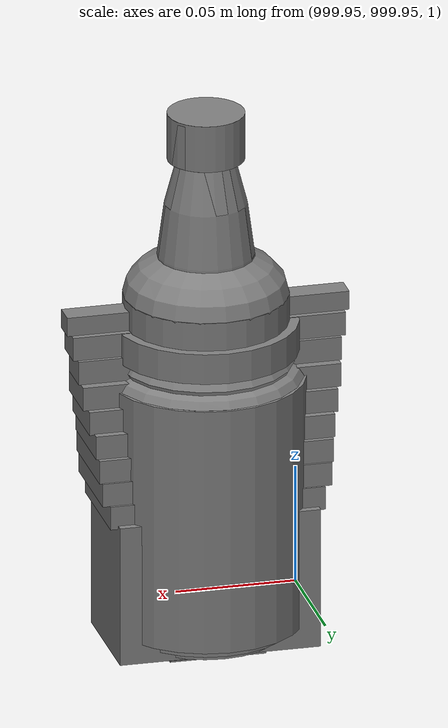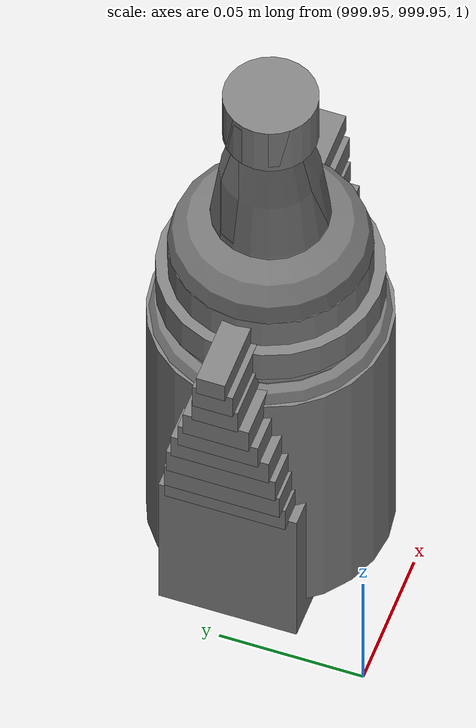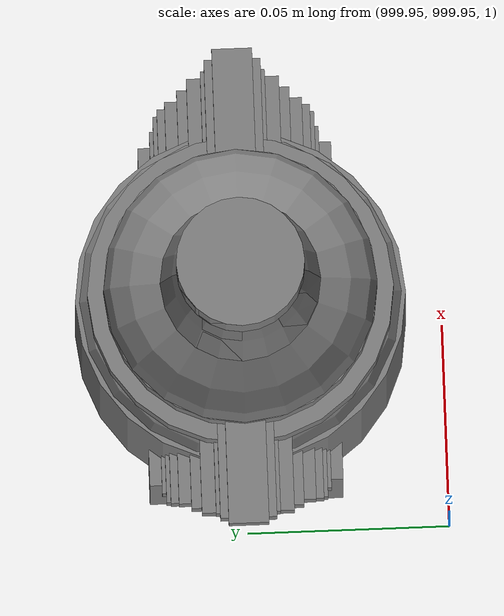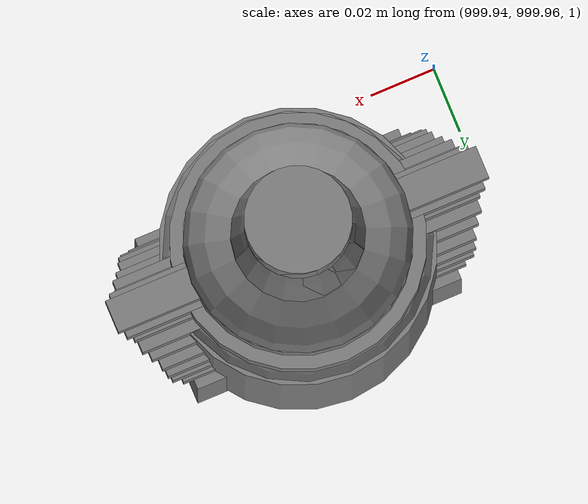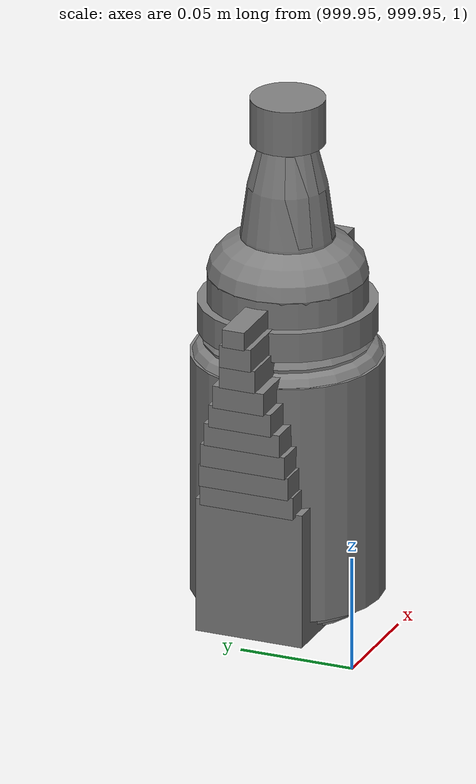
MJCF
<mujoco>
    <option gravity="0.000000000 0.000000000 -9.810000420" timestep="0.0166666" integrator="implicitfast" density="1.225" viscosity="1.8000001e-05" noslip_iterations="10" iterations="100" sdf_iterations="50">
        <flag multiccd="disable"/>
    </option>
    <size memory="1000M"/>
    <compiler coordinate="local"/>
    <worldbody>
        <light cutoff="30" pos="0 1 1" dir="0 -1 -2"/>
        <light cutoff="30" pos="0 -1 1" dir="0 1 -2"/>
        <body pos="0.000000000 0.000000000 0.000000000" euler="0.000000000 0.000000000 0.000000000" name="Interactive Objects_Interactive Objects"/>
        <body pos="-2.021729231 6.601751328 1.732057929" euler="-97.615066528 10.012110710 -138.892913818" mocap="true" name="spotlight3_SpotLight"/>
        <body pos="-1.787590384 5.883861065 1.726365805" euler="56.243133545 -13.055694580 -11.383227348" mocap="true" name="spotlight2_SpotLight"/>
        <body pos="-2.296195507 5.836155891 1.713086128" euler="-106.386398315 22.234432220 9.459137917" mocap="true" name="spotlight5_SpotLight"/>
        <body pos="1000.000000000 1000.000000000 1.000000000" euler="0.000000000 0.000000000 0.000000000" name="openloong_gripper_2f85_fix_base_usda_can">
            <geom contype="1" conaffinity="1" density="1000" type="cylinder" material="" rgba="0.500000000 0.500000000 0.500000000 1.000000000" solimp="0.899999976 0.949999988 0.001000000" friction="1.000000000 0.005000000 0.000100000" solref="0.020000000 1.000000000" margin="0" condim="3" group="0" pos="0.000000000 0.000000000 0.079676986" quat="1.000000000 0.000000000 0.000000000 0.000000000" size="0.034000002 0.071999997 1.000000000" name="openloong_gripper_2f85_fix_base_usda_geom_14FE3224_F60B_42C4_9F3E_E2649A7E2570"/>
            <geom contype="1" conaffinity="1" density="1000" type="ellipsoid" material="" rgba="0.500000000 0.500000000 0.500000000 1.000000000" solimp="0.899999976 0.949999988 0.001000000" friction="1.000000000 0.005000000 0.000100000" solref="0.020000000 1.000000000" margin="0" condim="3" group="0" pos="0.000000000 0.000000000 0.151854277" quat="1.000000000 0.000000000 0.000000000 0.000000000" size="0.034000002 0.034000002 0.020000000" name="openloong_gripper_2f85_fix_base_usda_geom_8C4200F7_A55A_48DE_AB4F_56A427B9CA56"/>
            <geom contype="1" conaffinity="1" density="1000" type="box" material="" rgba="0.500000000 0.500000000 0.500000000 1.000000000" solimp="0.899999976 0.949999988 0.001000000" friction="1.000000000 0.005000000 0.000100000" solref="0.020000000 1.000000000" margin="0" condim="3" group="0" pos="0.000000000 0.000000000 0.004777670" quat="1.000000000 0.000000000 0.000000000 0.000000000" size="0.020000000 0.020000000 0.005000000" name="openloong_gripper_2f85_fix_base_usda_geom_F718B64B_437E_4681_9E87_1F8BEDDB5A23"/>
            <freejoint name="openloong_gripper_2f85_fix_base_usda_can_joint"/>
            <site size="0.005000000 0.005000000 0.005000000" rgba="0.500000000 0.500000000 0.500000000 1.000000000" pos="0.000000000 0.000000000 0.000000000" quat="1.000000000 0.000000000 0.000000000 0.000000000" group="0" type="sphere" name="openloong_gripper_2f85_fix_base_usda_cansite"/>
        </body>
        <body pos="1000.000000000 1000.000000000 1.000000000" euler="0.000000000 0.000000000 0.000000000" name="openloong_gripper_2f85_fix_base_usda_bottle_red">
            <geom contype="1" conaffinity="1" density="1000" type="ellipsoid" material="" rgba="0.500000000 0.500000000 0.500000000 1.000000000" solimp="0.899999976 0.949999988 0.001000000" friction="1.000000000 0.005000000 0.000100000" solref="0.020000000 1.000000000" margin="0" condim="3" group="0" pos="0.000000000 0.000000000 0.144284487" quat="1.000000000 0.000000000 0.000000000 0.000000000" size="0.021000000 0.021000000 0.079999998" name="openloong_gripper_2f85_fix_base_usda_geom_EC6E1CC6_C920_4429_9D63_0DCC309BC007"/>
            <geom contype="1" conaffinity="1" density="1000" type="cylinder" material="" rgba="0.500000000 0.500000000 0.500000000 1.000000000" solimp="0.899999976 0.949999988 0.001000000" friction="1.000000000 0.005000000 0.000100000" solref="0.020000000 1.000000000" margin="0" condim="3" group="0" pos="0.000000000 0.000000000 0.220618963" quat="1.000000000 0.000000000 0.000000000 0.000000000" size="0.016000001 0.010000000 1.000000000" name="openloong_gripper_2f85_fix_base_usda_geom_096D0356_33A3_4EE0_A217_E9794F5ACD07"/>
            <geom contype="1" conaffinity="1" density="1000" type="ellipsoid" material="" rgba="0.500000000 0.500000000 0.500000000 1.000000000" solimp="0.899999976 0.949999988 0.001000000" friction="1.000000000 0.005000000 0.000100000" solref="0.020000000 1.000000000" margin="0" condim="3" group="0" pos="0.000000000 0.000000000 0.118945479" quat="1.000000000 0.000000000 0.000000000 0.000000000" size="0.030999999 0.030999999 0.029999999" name="openloong_gripper_2f85_fix_base_usda_geom_FD30A453_B650_49CD_A863_9424A82EDE5C"/>
            <geom contype="1" conaffinity="1" density="1000" type="box" material="" rgba="0.500000000 0.500000000 0.500000000 1.000000000" solimp="0.899999976 0.949999988 0.001000000" friction="1.000000000 0.005000000 0.000100000" solref="0.020000000 1.000000000" margin="0" condim="3" group="0" pos="0.000000000 0.000000000 0.002189159" quat="1.000000000 0.000000000 0.000000000 0.000000000" size="0.020000000 0.020000000 0.003000000" name="openloong_gripper_2f85_fix_base_usda_geom_7819CDC8_D2A3_47A7_ABF8_0445E576C739"/>
            <geom contype="1" conaffinity="1" density="1000" type="cylinder" material="" rgba="0.500000000 0.500000000 0.500000000 1.000000000" solimp="0.899999976 0.949999988 0.001000000" friction="1.000000000 0.005000000 0.000100000" solref="0.020000000 1.000000000" margin="0" condim="3" group="0" pos="0.000000000 -0.000366211 0.060884237" quat="1.000000000 0.000000000 0.000000000 0.000000000" size="0.030999999 0.057999998 1.000000000" name="openloong_gripper_2f85_fix_base_usda_geom_09A4D48B_4F9B_4F94_969F_47CFA1D3D5F5"/>
            <freejoint name="openloong_gripper_2f85_fix_base_usda_bottle_red_joint"/>
            <site size="0.005000000 0.005000000 0.005000000" rgba="0.500000000 0.500000000 0.500000000 1.000000000" pos="0.000000000 0.000000000 0.000000000" quat="0.999961913 0.008726535 0.000000000 0.000000000" group="0" type="sphere" name="openloong_gripper_2f85_fix_base_usda_bottle_redsite"/>
        </body>
        <body pos="1000.000000000 1000.000000000 1.000000000" euler="0.000000000 0.000000000 0.000000000" name="openloong_gripper_2f85_fix_base_usda_jar_01">
            <geom contype="1" conaffinity="1" density="1000" type="box" material="" rgba="0.500000000 0.500000000 0.500000000 1.000000000" solimp="0.899999976 0.949999988 0.001000000" friction="1.000000000 0.005000000 0.000100000" solref="0.020000000 1.000000000" margin="0" condim="3" group="0" pos="0.000000000 0.000000000 0.006158113" quat="1.000000000 0.000000000 0.000000000 0.000000000" size="0.020000000 0.020000000 0.005000000" name="openloong_gripper_2f85_fix_base_usda_geom_642FD352_A8C1_4723_8797_2F956EA595D3"/>
            <geom contype="1" conaffinity="1" density="1000" type="cylinder" material="" rgba="0.500000000 0.500000000 0.500000000 1.000000000" solimp="0.899999976 0.949999988 0.001000000" friction="1.000000000 0.005000000 0.000100000" solref="0.020000000 1.000000000" margin="0" condim="3" group="0" pos="0.000000000 0.000000000 0.062744498" quat="1.000000000 0.000000000 0.000000000 0.000000000" size="0.041000001 0.052999999 1.000000000" name="openloong_gripper_2f85_fix_base_usda_geom_ED22983E_513E_443B_B161_FE6893622CCA"/>
            <geom contype="1" conaffinity="1" density="1000" type="ellipsoid" material="" rgba="0.500000000 0.500000000 0.500000000 1.000000000" solimp="0.899999976 0.949999988 0.001000000" friction="1.000000000 0.005000000 0.000100000" solref="0.020000000 1.000000000" margin="0" condim="3" group="0" pos="0.000000000 0.000000000 0.122252703" quat="1.000000000 0.000000000 0.000000000 0.000000000" size="0.035999998 0.035999998 0.010000000" name="openloong_gripper_2f85_fix_base_usda_geom_1544435E_45F2_4967_A892_335DDA5714D2"/>
            <geom contype="1" conaffinity="1" density="1000" type="cylinder" material="" rgba="0.500000000 0.500000000 0.500000000 1.000000000" solimp="0.899999976 0.949999988 0.001000000" friction="1.000000000 0.005000000 0.000100000" solref="0.020000000 1.000000000" margin="0" condim="3" group="0" pos="0.000000000 0.000000000 0.015747190" quat="1.000000000 0.000000000 0.000000000 0.000000000" size="0.035000000 0.010000000 1.000000000" name="openloong_gripper_2f85_fix_base_usda_geom_7672830A_D0E9_4197_8E99_639597A5C44F"/>
            <geom contype="1" conaffinity="1" density="1000" type="ellipsoid" material="" rgba="0.500000000 0.500000000 0.500000000 1.000000000" solimp="0.899999976 0.949999988 0.001000000" friction="1.000000000 0.005000000 0.000100000" solref="0.020000000 1.000000000" margin="0" condim="3" group="0" pos="0.000000000 0.000000000 0.115815401" quat="1.000000000 0.000000000 0.000000000 0.000000000" size="0.039999999 0.039999999 0.010000000" name="openloong_gripper_2f85_fix_base_usda_geom_55EF297C_AF06_41CC_8EAF_362FF52AC9D9"/>
            <geom contype="1" conaffinity="1" density="1000" type="cylinder" material="" rgba="0.500000000 0.500000000 0.500000000 1.000000000" solimp="0.899999976 0.949999988 0.001000000" friction="1.000000000 0.005000000 0.000100000" solref="0.020000000 1.000000000" margin="0" condim="3" group="0" pos="0.000000000 0.000000000 0.133183479" quat="1.000000000 0.000000000 0.000000000 0.000000000" size="0.037999999 0.006500000 1.000000000" name="openloong_gripper_2f85_fix_base_usda_geom_DD670A63_1F7F_49BF_BE27_265177D25B8E"/>
            <freejoint name="openloong_gripper_2f85_fix_base_usda_jar_01_joint"/>
            <site size="0.005000000 0.005000000 0.005000000" rgba="0.500000000 0.500000000 0.500000000 1.000000000" pos="0.000000000 0.000000000 0.000000000" quat="1.000000000 0.000000000 0.000000000 0.000000000" group="0" type="sphere" name="openloong_gripper_2f85_fix_base_usda_jar_01site"/>
        </body>
        <body pos="1000.000000000 1000.000000000 1.000000000" euler="0.000000000 0.000000000 0.000000000" name="openloong_gripper_2f85_fix_base_usda_salt">
            <geom contype="1" conaffinity="1" density="1000" type="box" material="" rgba="0.500000000 0.500000000 0.500000000 1.000000000" solimp="0.899999976 0.949999988 0.001000000" friction="1.000000000 0.005000000 0.000100000" solref="0.020000000 1.000000000" margin="0" condim="3" group="0" pos="0.000305176 0.000000000 0.084862232" quat="1.000000000 0.000000000 0.000000000 0.000000000" size="0.048999999 0.018999999 0.005000000" name="openloong_gripper_2f85_fix_base_usda_geom_C473AA38_082A_497B_BFE9_C7580260E5AF"/>
            <geom contype="1" conaffinity="1" density="1000" type="box" material="" rgba="0.500000000 0.500000000 0.500000000 1.000000000" solimp="0.899999976 0.949999988 0.001000000" friction="1.000000000 0.005000000 0.000100000" solref="0.020000000 1.000000000" margin="0" condim="3" group="0" pos="0.000305176 0.000000000 0.104564309" quat="1.000000000 0.000000000 0.000000000 0.000000000" size="0.052000001 0.014000000 0.005000000" name="openloong_gripper_2f85_fix_base_usda_geom_CBDEE509_DD2F_48C6_A418_3719309DED9D"/>
            <geom contype="1" conaffinity="1" density="1000" type="box" material="" rgba="0.500000000 0.500000000 0.500000000 1.000000000" solimp="0.899999976 0.949999988 0.001000000" friction="1.000000000 0.005000000 0.000100000" solref="0.020000000 1.000000000" margin="0" condim="3" group="0" pos="0.000305176 0.000000000 0.114487171" quat="1.000000000 0.000000000 0.000000000 0.000000000" size="0.054000001 0.011500000 0.005000000" name="openloong_gripper_2f85_fix_base_usda_geom_4E37078A_3978_43CB_9F8D_D0841988F206"/>
            <geom contype="1" conaffinity="1" density="1000" type="box" material="" rgba="0.500000000 0.500000000 0.500000000 1.000000000" solimp="0.899999976 0.949999988 0.001000000" friction="1.000000000 0.005000000 0.000100000" solref="0.020000000 1.000000000" margin="0" condim="3" group="0" pos="0.000305176 0.000000000 0.075103164" quat="1.000000000 0.000000000 0.000000000 0.000000000" size="0.048000000 0.020000000 0.005000000" name="openloong_gripper_2f85_fix_base_usda_geom_17CFA004_2DCC_4172_88EC_8F9983F8FA41"/>
            <geom contype="1" conaffinity="1" density="1000" type="box" material="" rgba="0.500000000 0.500000000 0.500000000 1.000000000" solimp="0.899999976 0.949999988 0.001000000" friction="1.000000000 0.005000000 0.000100000" solref="0.020000000 1.000000000" margin="0" condim="3" group="0" pos="0.000305176 0.000000000 0.134892464" quat="1.000000000 0.000000000 0.000000000 0.000000000" size="0.057000000 0.007000000 0.005000000" name="openloong_gripper_2f85_fix_base_usda_geom_BBB900CE_819C_4F82_9A68_BF054BF589C9"/>
            <geom contype="1" conaffinity="1" density="1000" type="box" material="" rgba="0.500000000 0.500000000 0.500000000 1.000000000" solimp="0.899999976 0.949999988 0.001000000" friction="1.000000000 0.005000000 0.000100000" solref="0.020000000 1.000000000" margin="0" condim="3" group="0" pos="0.000305176 0.000000000 0.094920278" quat="1.000000000 0.000000000 0.000000000 0.000000000" size="0.050000001 0.017000001 0.005000000" name="openloong_gripper_2f85_fix_base_usda_geom_27AC847E_BEC6_4C7E_A6D0_DEF854785908"/>
            <geom contype="1" conaffinity="1" density="1000" type="box" material="" rgba="0.500000000 0.500000000 0.500000000 1.000000000" solimp="0.899999976 0.949999988 0.001000000" friction="1.000000000 0.005000000 0.000100000" solref="0.020000000 1.000000000" margin="0" condim="3" group="0" pos="0.000305176 0.000000000 0.065204859" quat="1.000000000 0.000000000 0.000000000 0.000000000" size="0.045000002 0.021000000 0.005000000" name="openloong_gripper_2f85_fix_base_usda_geom_C41B1476_C4C0_48CF_9A00_65B11478E352"/>
            <geom contype="1" conaffinity="1" density="1000" type="box" material="" rgba="0.500000000 0.500000000 0.500000000 1.000000000" solimp="0.899999976 0.949999988 0.001000000" friction="1.000000000 0.005000000 0.000100000" solref="0.020000000 1.000000000" margin="0" condim="3" group="0" pos="0.000305176 0.000000000 0.144135714" quat="1.000000000 0.000000000 0.000000000 0.000000000" size="0.059000000 0.005000000 0.004000000" name="openloong_gripper_2f85_fix_base_usda_geom_86831F43_8ECC_429A_851D_58A8DAF1B82C"/>
            <geom contype="1" conaffinity="1" density="1000" type="box" material="" rgba="0.500000000 0.500000000 0.500000000 1.000000000" solimp="0.899999976 0.949999988 0.001000000" friction="1.000000000 0.005000000 0.000100000" solref="0.020000000 1.000000000" margin="0" condim="3" group="0" pos="0.000000000 0.000000000 0.031593561" quat="1.000000000 0.000000000 0.000000000 0.000000000" size="0.041999999 0.024000000 0.029999999" name="openloong_gripper_2f85_fix_base_usda_geom_FC83613A_3AE3_4A95_A647_51B5AC51B9BB"/>
            <geom contype="1" conaffinity="1" density="1000" type="box" material="" rgba="0.500000000 0.500000000 0.500000000 1.000000000" solimp="0.899999976 0.949999988 0.001000000" friction="1.000000000 0.005000000 0.000100000" solref="0.020000000 1.000000000" margin="0" condim="3" group="0" pos="0.000305176 0.000000000 0.124608755" quat="1.000000000 0.000000000 0.000000000 0.000000000" size="0.055000000 0.008000000 0.005000000" name="openloong_gripper_2f85_fix_base_usda_geom_278E12D5_F176_43BE_A30C_E40FA0E73BBF"/>
            <freejoint name="openloong_gripper_2f85_fix_base_usda_salt_joint"/>
            <site size="0.005000000 0.005000000 0.005000000" rgba="0.500000000 0.500000000 0.500000000 1.000000000" pos="0.000000000 0.000000000 0.000000000" quat="1.000000000 0.000000000 0.000000000 0.000000000" group="0" type="sphere" name="openloong_gripper_2f85_fix_base_usda_saltsite"/>
        </body>
        <body pos="1000.000000000 1000.000000000 1.000000000" euler="0.000000000 0.000000000 0.000000000" name="openloong_gripper_2f85_fix_base_usda_bottle_blue">
            <geom contype="1" conaffinity="1" density="1000" type="ellipsoid" material="" rgba="0.500000000 0.500000000 0.500000000 1.000000000" solimp="0.899999976 0.949999988 0.001000000" friction="1.000000000 0.005000000 0.000100000" solref="0.020000000 1.000000000" margin="0" condim="3" group="0" pos="0.000000000 0.000000000 0.118920922" quat="1.000000000 0.000000000 0.000000000 0.000000000" size="0.030999999 0.030999999 0.029999999" name="openloong_gripper_2f85_fix_base_usda_geom_D555D084_F1AF_4820_B195_6D59F61DF330"/>
            <geom contype="1" conaffinity="1" density="1000" type="box" material="" rgba="0.500000000 0.500000000 0.500000000 1.000000000" solimp="0.899999976 0.949999988 0.001000000" friction="1.000000000 0.005000000 0.000100000" solref="0.020000000 1.000000000" margin="0" condim="3" group="0" pos="0.000000000 0.000000000 0.002164602" quat="1.000000000 0.000000000 0.000000000 0.000000000" size="0.020000000 0.020000000 0.003000000" name="openloong_gripper_2f85_fix_base_usda_geom_857DD66E_1D73_4FC9_B9D2_717054295725"/>
            <geom contype="1" conaffinity="1" density="1000" type="cylinder" material="" rgba="0.500000000 0.500000000 0.500000000 1.000000000" solimp="0.899999976 0.949999988 0.001000000" friction="1.000000000 0.005000000 0.000100000" solref="0.020000000 1.000000000" margin="0" condim="3" group="0" pos="0.000000000 -0.000366211 0.060859680" quat="1.000000000 0.000000000 0.000000000 0.000000000" size="0.030999999 0.057999998 1.000000000" name="openloong_gripper_2f85_fix_base_usda_geom_EF9C9719_1DE8_489D_86B4_84E513F181CB"/>
            <geom contype="1" conaffinity="1" density="1000" type="cylinder" material="" rgba="0.500000000 0.500000000 0.500000000 1.000000000" solimp="0.899999976 0.949999988 0.001000000" friction="1.000000000 0.005000000 0.000100000" solref="0.020000000 1.000000000" margin="0" condim="3" group="0" pos="0.000000000 0.000000000 0.220594406" quat="1.000000000 0.000000000 0.000000000 0.000000000" size="0.016000001 0.010000000 1.000000000" name="openloong_gripper_2f85_fix_base_usda_geom_34535498_6B2A_4BEC_A10B_5B0ACE5959C9"/>
            <geom contype="1" conaffinity="1" density="1000" type="ellipsoid" material="" rgba="0.500000000 0.500000000 0.500000000 1.000000000" solimp="0.899999976 0.949999988 0.001000000" friction="1.000000000 0.005000000 0.000100000" solref="0.020000000 1.000000000" margin="0" condim="3" group="0" pos="0.000000000 0.000000000 0.144259930" quat="1.000000000 0.000000000 0.000000000 0.000000000" size="0.021000000 0.021000000 0.079999998" name="openloong_gripper_2f85_fix_base_usda_geom_7BD0160C_A545_4DCC_9811_52FB9EFAF02F"/>
            <freejoint name="openloong_gripper_2f85_fix_base_usda_bottle_blue_joint"/>
            <site size="0.005000000 0.005000000 0.005000000" rgba="0.500000000 0.500000000 0.500000000 1.000000000" pos="0.000000000 0.000000000 0.000000000" quat="0.999961913 0.008726535 0.000000000 0.000000000" group="0" type="sphere" name="openloong_gripper_2f85_fix_base_usda_bottle_bluesite"/>
        </body>
        <body pos="0.000000000 0.000000000 0.000000000" euler="0.000000000 0.000000000 0.000000000" name=" Static Objects_ Static Objects">
            <geom contype="1" conaffinity="1" density="1000" type="box" material="" rgba="0.500000000 0.500000000 0.500000000 1.000000000" solimp="0.899999976 0.949999988 0.001000000" friction="1.000000000 0.005000000 0.000100000" solref="0.020000000 1.000000000" margin="0" condim="3" group="0" pos="-3.101639986 6.150595188 1.018643856" quat="1.000000000 0.000000000 0.000000000 0.000000000" size="0.050000001 0.579999983 1.019999981" name=" Static Objects_geom_8585D036_2FDD_4703_894B_F56157C9B763"/>
            <geom contype="1" conaffinity="1" density="1000" type="box" material="" rgba="0.500000000 0.500000000 0.500000000 1.000000000" solimp="0.899999976 0.949999988 0.001000000" friction="1.000000000 0.005000000 0.000100000" solref="0.020000000 1.000000000" margin="0" condim="3" group="0" pos="-2.825197220 6.153595448 1.115278244" quat="0.707107067 0.000000000 0.000000000 0.707106471" size="0.550000012 0.239999995 0.025000000" name=" Static Objects_geom_3A59E806_9449_4A0F_835D_A5CF7B63CB55"/>
            <geom contype="1" conaffinity="1" density="1000" type="box" material="" rgba="0.500000000 0.500000000 0.500000000 1.000000000" solimp="0.899999976 0.949999988 0.001000000" friction="1.000000000 0.005000000 0.000100000" solref="0.020000000 1.000000000" margin="0" condim="3" group="0" pos="-2.825197220 6.153595448 0.097434282" quat="0.707107067 0.000000000 0.000000000 0.707106471" size="0.550000012 0.239999995 0.098999999" name=" Static Objects_geom_4B296615_03B4_4BD7_9CF4_692E3C408DC8"/>
            <geom contype="1" conaffinity="1" density="1000" type="box" material="" rgba="0.500000000 0.500000000 0.500000000 1.000000000" solimp="0.899999976 0.949999988 0.001000000" friction="1.000000000 0.005000000 0.000100000" solref="0.020000000 1.000000000" margin="0" condim="3" group="0" pos="-6.293097973 6.153595448 1.114443064" quat="0.707107067 0.000000000 0.000000000 0.707106471" size="0.529999971 3.134999990 0.025000000" name=" Static Objects_geom_48936157_B4CE_491D_8F00_2A4D73A75401"/>
            <geom contype="1" conaffinity="1" density="1000" type="box" material="" rgba="0.500000000 0.500000000 0.500000000 1.000000000" solimp="0.899999976 0.949999988 0.001000000" friction="1.000000000 0.005000000 0.000100000" solref="0.020000000 1.000000000" margin="0" condim="3" group="0" pos="-6.286010742 6.153595448 0.096129179" quat="0.707107067 0.000000000 0.000000000 0.707106471" size="0.529999971 3.134999990 0.098999999" name=" Static Objects_geom_76749141_7E89_4123_B123_2464A43EE21B"/>
            <geom contype="1" conaffinity="1" density="1000" type="box" material="" rgba="0.500000000 0.500000000 0.500000000 1.000000000" solimp="0.899999976 0.949999988 0.001000000" friction="1.000000000 0.005000000 0.000100000" solref="0.020000000 1.000000000" margin="0" condim="3" group="0" pos="-2.825197220 6.153595448 1.563861728" quat="0.707107067 0.000000000 0.000000000 0.707106471" size="0.550000012 0.239999995 0.025000000" name=" Static Objects_geom_A58EF467_D18F_447C_96AB_0A84F05C0326"/>
            <geom contype="1" conaffinity="1" density="1000" type="box" material="" rgba="0.500000000 0.500000000 0.500000000 1.000000000" solimp="0.899999976 0.949999988 0.001000000" friction="1.000000000 0.005000000 0.000100000" solref="0.020000000 1.000000000" margin="0" condim="3" group="0" pos="-6.311686516 6.153595448 1.018643856" quat="0.707107067 0.000000000 0.000000000 0.707106471" size="0.050000001 3.150000095 1.019999981" name=" Static Objects_geom_BC1436B3_58D1_436F_86E9_29744838FCF4"/>
            <geom contype="1" conaffinity="1" density="1000" type="box" material="" rgba="0.500000000 0.500000000 0.500000000 1.000000000" solimp="0.899999976 0.949999988 0.001000000" friction="1.000000000 0.005000000 0.000100000" solref="0.020000000 1.000000000" margin="0" condim="3" group="0" pos="-2.825197220 6.153595448 0.629031777" quat="0.707107067 0.000000000 0.000000000 0.707106471" size="0.550000012 0.239999995 0.025000000" name=" Static Objects_geom_66402944_4D73_4116_B539_34A43F647055"/>
            <geom contype="1" conaffinity="1" density="1000" type="box" material="" rgba="0.500000000 0.500000000 0.500000000 1.000000000" solimp="0.899999976 0.949999988 0.001000000" friction="1.000000000 0.005000000 0.000100000" solref="0.020000000 1.000000000" margin="0" condim="3" group="0" pos="-6.286010742 6.153595448 1.563861728" quat="0.707107067 0.000000000 0.000000000 0.707106471" size="0.529999971 3.134999990 0.025000000" name=" Static Objects_geom_C823D425_14A5_4A16_A586_429632C5A73A"/>
            <geom contype="1" conaffinity="1" density="1000" type="box" material="" rgba="0.500000000 0.500000000 0.500000000 1.000000000" solimp="0.899999976 0.949999988 0.001000000" friction="1.000000000 0.005000000 0.000100000" solref="0.020000000 1.000000000" margin="0" condim="3" group="0" pos="-6.286010742 6.153595448 0.629031777" quat="0.707107067 0.000000000 0.000000000 0.707106471" size="0.529999971 3.134999990 0.025000000" name=" Static Objects_geom_DD0114C8_AC00_4E46_83B5_788D330D8D84"/>
            <geom contype="1" conaffinity="1" density="1000" type="box" material="" rgba="0.500000000 0.500000000 0.500000000 1.000000000" solimp="0.899999976 0.949999988 0.001000000" friction="1.000000000 0.005000000 0.000100000" solref="0.020000000 1.000000000" margin="0" condim="3" group="0" pos="-7.719123363 2.867671013 1.173410416" quat="1.000000000 0.000000000 0.000000000 0.000000000" size="0.250000000 0.250000000 0.079999998" name=" Static Objects_geom_7EAEEB6D_0A8F_49B7_929E_B10CD49EDF61"/>
            <geom contype="1" conaffinity="1" density="1000" type="box" material="" rgba="0.500000000 0.500000000 0.500000000 1.000000000" solimp="0.899999976 0.949999988 0.001000000" friction="1.000000000 0.005000000 0.000100000" solref="0.020000000 1.000000000" margin="0" condim="3" group="0" pos="-7.408766270 3.088089943 1.776644945" quat="0.928051054 0.000000000 0.000000000 0.372453064" size="0.050000001 0.100000001 0.050000001" name=" Static Objects_geom_9C13D13F_C95F_423F_9179_F1A8561B592D"/>
            <geom contype="1" conaffinity="1" density="1000" type="box" material="" rgba="0.500000000 0.500000000 0.500000000 1.000000000" solimp="0.899999976 0.949999988 0.001000000" friction="1.000000000 0.005000000 0.000100000" solref="0.020000000 1.000000000" margin="0" condim="3" group="0" pos="-7.719123363 2.958004713 1.530241251" quat="1.000000000 0.000000000 0.000000000 0.000000000" size="0.250000000 0.159999996 0.280000001" name=" Static Objects_geom_5F82477A_EB9B_446F_8AC0_2B04FA2E6ABA"/>
            <geom contype="1" conaffinity="1" density="1000" type="cylinder" material="" rgba="0.500000000 0.500000000 0.500000000 1.000000000" solimp="0.899999976 0.949999988 0.001000000" friction="1.000000000 0.005000000 0.000100000" solref="0.020000000 1.000000000" margin="0" condim="3" group="0" pos="-7.427312374 3.069516420 1.502544641" quat="0.928051054 0.000000000 0.000000000 0.372453064" size="0.015000000 0.230000004 0.100000001" name=" Static Objects_geom_DA9609BB_AE4B_455E_9015_549DF6C98414"/>
            <geom contype="1" conaffinity="1" density="1000" type="box" material="" rgba="0.500000000 0.500000000 0.500000000 1.000000000" solimp="0.899999976 0.949999988 0.001000000" friction="1.000000000 0.005000000 0.000100000" solref="0.020000000 1.000000000" margin="0" condim="3" group="0" pos="-7.437745571 3.067511320 1.289965630" quat="1.000000000 0.000000000 0.000000000 0.000000000" size="0.029999999 0.020000000 0.020000000" name=" Static Objects_geom_1016721C_2AFD_4AF1_B81A_1E60488CEEDC"/>
            <geom contype="1" conaffinity="1" density="1000" type="box" material="" rgba="0.500000000 0.500000000 0.500000000 1.000000000" solimp="0.899999976 0.949999988 0.001000000" friction="1.000000000 0.005000000 0.000100000" solref="0.020000000 1.000000000" margin="0" condim="3" group="0" pos="-9.058088303 6.434794426 1.209077358" quat="1.000000000 0.000000000 0.000000000 0.000000000" size="0.250000000 0.100000001 0.070000000" name=" Static Objects_geom_823CF684_2A49_4BEB_A93A_0BB297FF0BFC"/>
            <geom contype="1" conaffinity="1" density="1000" type="box" material="" rgba="0.500000000 0.500000000 0.500000000 1.000000000" solimp="0.899999976 0.949999988 0.001000000" friction="1.000000000 0.005000000 0.000100000" solref="0.020000000 1.000000000" margin="0" condim="3" group="0" pos="-7.886891365 6.459744930 0.352518857" quat="1.000000000 0.000000000 0.000000000 0.000000000" size="1.500000000 0.200000003 0.150000006" name=" Static Objects_geom_578BDDC8_C4ED_493C_850D_FA0D2606B62E"/>
            <geom contype="1" conaffinity="1" density="1000" type="box" material="" rgba="0.500000000 0.500000000 0.500000000 1.000000000" solimp="0.899999976 0.949999988 0.001000000" friction="1.000000000 0.005000000 0.000100000" solref="0.020000000 1.000000000" margin="0" condim="3" group="0" pos="-9.237723351 6.464855671 1.209077358" quat="1.000000000 0.000000000 0.000000000 0.000000000" size="0.100000001 0.100000001 0.070000000" name=" Static Objects_geom_1AE2898E_4094_423C_AC78_EFF4A3E4C766"/>
            <geom contype="1" conaffinity="1" density="1000" type="box" material="" rgba="0.500000000 0.500000000 0.500000000 1.000000000" solimp="0.899999976 0.949999988 0.001000000" friction="1.000000000 0.005000000 0.000100000" solref="0.020000000 1.000000000" margin="0" condim="3" group="0" pos="-6.924745083 6.362090111 1.214329123" quat="1.000000000 0.000000000 0.000000000 0.000000000" size="0.200000003 0.100000001 0.075000003" name=" Static Objects_geom_F0E9B09F_46B0_442D_A2B3_F56AEE725AF8"/>
            <geom contype="1" conaffinity="1" density="1000" type="box" material="" rgba="0.500000000 0.500000000 0.500000000 1.000000000" solimp="0.899999976 0.949999988 0.001000000" friction="1.000000000 0.005000000 0.000100000" solref="0.020000000 1.000000000" margin="0" condim="3" group="0" pos="-4.407354832 6.459744930 1.292199373" quat="1.000000000 0.000000000 0.000000000 0.000000000" size="1.240000010 0.200000003 0.150000006" name=" Static Objects_geom_2A6E77AD_D0C4_4E01_93CD_99A599A20E01"/>
            <geom contype="1" conaffinity="1" density="1000" type="box" material="" rgba="0.500000000 0.500000000 0.500000000 1.000000000" solimp="0.899999976 0.949999988 0.001000000" friction="1.000000000 0.005000000 0.000100000" solref="0.020000000 1.000000000" margin="0" condim="3" group="0" pos="-5.611940861 6.318420410 0.350975692" quat="1.000000000 0.000000000 0.000000000 0.000000000" size="0.699999988 0.100000001 0.150000006" name=" Static Objects_geom_FACA92C5_C20E_47B5_B8C0_75A5F6456553"/>
            <geom contype="1" conaffinity="1" density="1000" type="box" material="" rgba="0.500000000 0.500000000 0.500000000 1.000000000" solimp="0.899999976 0.949999988 0.001000000" friction="1.000000000 0.005000000 0.000100000" solref="0.020000000 1.000000000" margin="0" condim="3" group="0" pos="-6.300771236 6.459744930 1.744376063" quat="1.000000000 0.000000000 0.000000000 0.000000000" size="3.000000000 0.200000003 0.150000006" name=" Static Objects_geom_E694348B_1AF5_46D9_A250_878DE2694B75"/>
            <geom contype="1" conaffinity="1" density="1000" type="box" material="" rgba="0.500000000 0.500000000 0.500000000 1.000000000" solimp="0.899999976 0.949999988 0.001000000" friction="1.000000000 0.005000000 0.000100000" solref="0.020000000 1.000000000" margin="0" condim="3" group="0" pos="-6.751636982 6.459744930 0.800981164" quat="1.000000000 0.000000000 0.000000000 0.000000000" size="2.200000048 0.200000003 0.150000006" name=" Static Objects_geom_D4F1299C_8D34_4F5A_89E4_33BA4D8AA2EF"/>
            <geom contype="1" conaffinity="1" density="1000" type="box" material="" rgba="0.500000000 0.500000000 0.500000000 1.000000000" solimp="0.899999976 0.949999988 0.001000000" friction="1.000000000 0.005000000 0.000100000" solref="0.020000000 1.000000000" margin="0" condim="3" group="0" pos="-8.844120979 6.464855671 1.209077358" quat="1.000000000 0.000000000 0.000000000 0.000000000" size="0.100000001 0.100000001 0.070000000" name=" Static Objects_geom_7149863F_7ACE_450C_86AD_F1CBB9125DD2"/>
            <geom contype="1" conaffinity="1" density="1000" type="box" material="" rgba="0.500000000 0.500000000 0.500000000 1.000000000" solimp="0.899999976 0.949999988 0.001000000" friction="1.000000000 0.005000000 0.000100000" solref="0.020000000 1.000000000" margin="0" condim="3" group="0" pos="-6.098561764 6.327973843 1.292199373" quat="1.000000000 0.000000000 0.000000000 0.000000000" size="0.500000000 0.100000001 0.150000006" name=" Static Objects_geom_75FB749B_37C9_40C1_A0BE_9E6EE28D97C4"/>
            <geom contype="1" conaffinity="1" density="1000" type="box" material="" rgba="0.500000000 0.500000000 0.500000000 1.000000000" solimp="0.899999976 0.949999988 0.001000000" friction="1.000000000 0.005000000 0.000100000" solref="0.020000000 1.000000000" margin="0" condim="3" group="0" pos="-6.824534416 6.447464466 1.212718010" quat="1.000000000 0.000000000 0.000000000 0.000000000" size="0.100000001 0.100000001 0.075000003" name=" Static Objects_geom_C9F9934B_2CB4_4691_B799_AA76511AB4D7"/>
            <geom contype="1" conaffinity="1" density="1000" type="box" material="" rgba="0.500000000 0.500000000 0.500000000 1.000000000" solimp="0.899999976 0.949999988 0.001000000" friction="1.000000000 0.005000000 0.000100000" solref="0.020000000 1.000000000" margin="0" condim="3" group="0" pos="-3.907610416 6.318625927 0.800981164" quat="1.000000000 0.000000000 0.000000000 0.000000000" size="0.500000000 0.100000001 0.150000006" name=" Static Objects_geom_5BB2042A_8813_4D63_B2DD_F8B7CF79D2EE"/>
            <geom contype="1" conaffinity="1" density="1000" type="box" material="" rgba="0.500000000 0.500000000 0.500000000 1.000000000" solimp="0.899999976 0.949999988 0.001000000" friction="1.000000000 0.005000000 0.000100000" solref="0.020000000 1.000000000" margin="0" condim="3" group="0" pos="-7.373087406 6.458900928 1.214329123" quat="1.000000000 0.000000000 0.000000000 0.000000000" size="0.250000000 0.200000003 0.075000003" name=" Static Objects_geom_F7B48AC8_5F5C_4FDA_BE74_7E28F0F0829B"/>
            <geom contype="1" conaffinity="1" density="1000" type="box" material="" rgba="0.500000000 0.500000000 0.500000000 1.000000000" solimp="0.899999976 0.949999988 0.001000000" friction="1.000000000 0.005000000 0.000100000" solref="0.020000000 1.000000000" margin="0" condim="3" group="0" pos="-4.035642624 6.459744930 0.352518857" quat="1.000000000 0.000000000 0.000000000 0.000000000" size="0.800000012 0.200000003 0.150000006" name=" Static Objects_geom_B8259508_B8D3_4C67_85BA_AF269843B81F"/>
            <geom contype="1" conaffinity="1" density="1000" type="box" material="" rgba="0.500000000 0.500000000 0.500000000 1.000000000" solimp="0.899999976 0.949999988 0.001000000" friction="1.000000000 0.005000000 0.000100000" solref="0.020000000 1.000000000" margin="0" condim="3" group="0" pos="-6.460197449 2.937205315 0.548931718" quat="1.000000000 0.000000000 0.000000000 0.000000000" size="2.650000095 0.430000007 0.550000012" name=" Static Objects_geom_79F4D43D_E5CF_47C5_8E8A_FB1588B8B5CE"/>
            <geom contype="1" conaffinity="1" density="1000" type="box" material="" rgba="0.500000000 0.500000000 0.500000000 1.000000000" solimp="0.899999976 0.949999988 0.001000000" friction="1.000000000 0.005000000 0.000100000" solref="0.020000000 1.000000000" margin="0" condim="3" group="0" pos="-4.240264893 1.327049494 0.549888909" quat="1.000000000 0.000000000 0.000000000 0.000000000" size="0.430000007 1.200000048 0.550000012" name=" Static Objects_geom_3959DDAC_44FB_41DF_8B8B_C6961F655E0F"/>
            <geom contype="1" conaffinity="1" density="1000" type="box" material="" rgba="0.500000000 0.500000000 0.500000000 1.000000000" solimp="0.899999976 0.949999988 0.001000000" friction="1.000000000 0.005000000 0.000100000" solref="0.020000000 1.000000000" margin="0" condim="3" group="0" pos="-8.830721855 2.096410990 0.549305558" quat="1.000000000 0.000000000 0.000000000 0.000000000" size="0.280000001 0.430000007 0.550000012" name=" Static Objects_geom_68ED6596_55B2_4831_88CC_ADD1455BD765"/>
            <geom contype="1" conaffinity="1" density="1000" type="plane" material="" rgba="0.500000000 0.500000000 0.500000000 1.000000000" solimp="0.899999976 0.949999988 0.001000000" friction="1.000000000 0.005000000 0.000100000" solref="0.020000000 1.000000000" margin="0" condim="3" group="0" pos="-6.000000000 10.399999619 0.000000000" quat="1.000000000 0.000000000 0.000000000 0.000000000" size="6.050000191 10.800000191 0.010000000" name=" Static Objects_geom_DC3323D1_0D86_4448_9D9B_6E8FB90496E3"/>
            <geom contype="1" conaffinity="1" density="1000" type="box" material="" rgba="0.500000000 0.500000000 0.500000000 1.000000000" solimp="0.899999976 0.949999988 0.001000000" friction="1.000000000 0.005000000 0.000100000" solref="0.020000000 1.000000000" margin="0" condim="3" group="0" pos="-6.000000000 0.035000000 2.000000000" quat="1.000000000 0.000000000 0.000000000 0.000000000" size="6.079999924 0.070000000 2.000000000" name=" Static Objects_geom_F31EE80D_8D59_41AC_9153_162C172883BE"/>
            <geom contype="1" conaffinity="1" density="1000" type="box" material="" rgba="0.500000000 0.500000000 0.500000000 1.000000000" solimp="0.899999976 0.949999988 0.001000000" friction="1.000000000 0.005000000 0.000100000" solref="0.020000000 1.000000000" margin="0" condim="3" group="0" pos="-6.000000000 20.159999847 2.000000000" quat="1.000000000 0.000000000 0.000000000 0.000000000" size="6.079999924 0.070000000 2.000000000" name=" Static Objects_geom_FE11DC19_3925_48CB_9D2C_82E363B5A4CA"/>
            <geom contype="1" conaffinity="1" density="1000" type="box" material="" rgba="0.500000000 0.500000000 0.500000000 1.000000000" solimp="0.899999976 0.949999988 0.001000000" friction="1.000000000 0.005000000 0.000100000" solref="0.020000000 1.000000000" margin="0" condim="3" group="0" pos="0.000000000 10.000000000 2.000000000" quat="1.000000000 0.000000000 0.000000000 0.000000000" size="0.070000000 10.500000000 2.000000000" name=" Static Objects_geom_FA4BE8DA_2641_4942_B544_2C5294312C02"/>
            <geom contype="1" conaffinity="1" density="1000" type="box" material="" rgba="0.500000000 0.500000000 0.500000000 1.000000000" solimp="0.899999976 0.949999988 0.001000000" friction="1.000000000 0.005000000 0.000100000" solref="0.020000000 1.000000000" margin="0" condim="3" group="0" pos="-12.050000191 10.000000000 2.000000000" quat="1.000000000 0.000000000 0.000000000 0.000000000" size="0.070000000 10.500000000 2.000000000" name=" Static Objects_geom_E8F0D738_BF57_4F52_AF97_964A7249694E"/>
        </body>
        <body pos="-3.510578632 3.403555870 -0.000000100" euler="0.000000000 0.000000000 40.200675964" name="openloong_gripper_2f85_fix_base_usda_PZ">
            <geom contype="1" conaffinity="1" density="1000" type="box" material="" rgba="0.500000000 0.500000000 0.500000000 1.000000000" solimp="0.899999976 0.949999988 0.001000000" friction="1.000000000 0.005000000 0.000100000" solref="0.020000000 1.000000000" margin="0" condim="3" group="0" pos="-0.047453165 0.056484699 0.373715430" quat="0.934750080 0.077914521 0.028795123 0.345459938" size="0.180000007 0.010000000 0.379999995" name="openloong_gripper_2f85_fix_base_usda_geom_40174CB9_6131_4696_AA51_F08AD4559003"/>
            <geom contype="1" conaffinity="1" density="1000" type="box" material="" rgba="0.500000000 0.500000000 0.500000000 1.000000000" solimp="0.899999976 0.949999988 0.001000000" friction="1.000000000 0.005000000 0.000100000" solref="0.020000000 1.000000000" margin="0" condim="3" group="0" pos="0.047452450 -0.054376602 0.374072611" quat="0.934387863 -0.082143910 -0.030358355 0.345326364" size="0.180000007 0.010000000 0.379999995" name="openloong_gripper_2f85_fix_base_usda_geom_5EA15639_0038_46FF_AED8_59CC253863B0"/>
            <freejoint name="openloong_gripper_2f85_fix_base_usda_PZ"/>
        </body>
        <body pos="-6.332345009 2.779978037 1.034067392" euler="0.000000000 0.000000000 0.000000000" name="openloong_gripper_2f85_fix_base_usda_basket">
            <geom contype="1" conaffinity="1" density="100000" type="box" material="" rgba="0.500000000 0.500000000 0.500000000 1.000000000" solimp="0.899999976 0.949999988 0.001000000" friction="1.000000000 0.899999976 0.000100000" solref="0.020000000 1.000000000" margin="0" condim="3" group="0" pos="-0.172339439 0.000000000 0.168361664" quat="0.706172407 -0.036353018 -0.036353093 0.706170976" size="0.200000003 0.006000000 0.108000003" name="openloong_gripper_2f85_fix_base_usda_geom_EECA97CB_2A79_4D9F_9E1F_FBBDA1D941BB"/>
            <geom contype="1" conaffinity="1" density="100000" type="box" material="" rgba="0.500000000 0.500000000 0.500000000 1.000000000" solimp="0.899999976 0.949999988 0.001000000" friction="1.000000000 0.899999976 0.000100000" solref="0.020000000 1.000000000" margin="0" condim="3" group="0" pos="-0.039724827 -0.188568115 0.167089701" quat="0.997537494 0.070135131 0.000000000 0.000000000" size="0.150000006 0.006000000 0.108000003" name="openloong_gripper_2f85_fix_base_usda_geom_580FCEEB_6C32_4F6B_8649_2D458C79262B"/>
            <geom contype="1" conaffinity="1" density="100000" type="box" material="" rgba="0.500000000 0.500000000 0.500000000 1.000000000" solimp="0.899999976 0.949999988 0.001000000" friction="1.000000000 0.899999976 0.000100000" solref="0.020000000 1.000000000" margin="0" condim="3" group="0" pos="-0.039724827 0.188377380 0.167089701" quat="0.997489929 -0.070808925 0.000000000 0.000000000" size="0.150000006 0.006000000 0.108000003" name="openloong_gripper_2f85_fix_base_usda_geom_DAAEB037_DC78_44F1_B6E9_B54960B2BE3C"/>
            <geom contype="1" conaffinity="1" density="100000" type="box" material="" rgba="0.500000000 0.500000000 0.500000000 1.000000000" solimp="0.899999976 0.949999988 0.001000000" friction="1.000000000 0.899999976 0.000100000" solref="0.020000000 1.000000000" margin="0" condim="3" group="0" pos="-0.039724827 0.000000000 0.068126202" quat="1.000000000 0.000000000 0.000000000 0.000000000" size="0.129999995 0.174999997 0.006000000" name="openloong_gripper_2f85_fix_base_usda_geom_377D89C9_FA08_4642_8DCA_D3F46A0ECEB2"/>
            <geom contype="1" conaffinity="1" density="100000" type="box" material="" rgba="0.500000000 0.500000000 0.500000000 1.000000000" solimp="0.899999976 0.949999988 0.001000000" friction="1.000000000 0.899999976 0.000100000" solref="0.020000000 1.000000000" margin="0" condim="3" group="0" pos="0.094372749 0.000000000 0.168361664" quat="0.706172049 0.036353335 0.036353379 0.706171215" size="0.200000003 0.006000000 0.108000003" name="openloong_gripper_2f85_fix_base_usda_geom_43A04918_A59C_4368_AB75_CC0D1E18D137"/>
            <freejoint name="openloong_gripper_2f85_fix_base_usda_basket_joint"/>
            <site size="0.005000000 0.005000000 0.005000000" rgba="0.500000000 0.500000000 0.500000000 1.000000000" pos="0.000000000 0.000000000 0.000000000" quat="1.000000000 0.000000000 0.000000000 0.000000000" group="0" type="sphere" name="openloong_gripper_2f85_fix_base_usda_basketsite"/>
        </body>
        <body pos="-2.436573029 6.404376507 0.137849092" euler="0.000000000 0.000000000 0.000000000" name="openloong_gripper_2f85_fix_base_usda_shoppingtrolley_01">
            <geom contype="1" conaffinity="1" density="1000" type="box" material="" rgba="0.500000000 0.500000000 0.500000000 1.000000000" solimp="0.899999976 0.949999988 0.001000000" friction="1.000000000 0.005000000 0.000100000" solref="0.020000000 1.000000000" margin="0" condim="3" group="0" pos="-0.169898406 -0.178061336 0.864131629" quat="0.916343808 -0.400392294 -0.000000045 0.000000030" size="0.017999999 0.022499999 0.089999996" name="openloong_gripper_2f85_fix_base_usda_geom_96431E80_4FC2_4B15_B108_45C425EACDF4"/>
            <geom contype="1" conaffinity="1" density="1000" type="box" material="" rgba="0.500000000 0.500000000 0.500000000 1.000000000" solimp="0.899999976 0.949999988 0.001000000" friction="1.000000000 0.005000000 0.000100000" solref="0.020000000 1.000000000" margin="0" condim="3" group="0" pos="-0.107458733 0.238907143 0.911498845" quat="0.634576976 0.622505128 -0.330067992 -0.317575932" size="0.017999999 0.022499999 0.035999998" name="openloong_gripper_2f85_fix_base_usda_geom_25667E40_3A05_4B89_8500_77BF88EA6DF8"/>
            <geom contype="1" conaffinity="1" density="1000" type="box" material="" rgba="0.500000000 0.500000000 0.500000000 1.000000000" solimp="0.899999976 0.949999988 0.001000000" friction="1.000000000 0.005000000 0.000100000" solref="0.020000000 1.000000000" margin="0" condim="3" group="0" pos="-0.005004787 0.248085022 0.912686050" quat="1.000000000 0.000000000 0.000000000 0.000000000" size="0.107999995 0.022499999 0.022499999" name="openloong_gripper_2f85_fix_base_usda_geom_78EC884D_CAE0_4AA8_89EE_2E4B817B4FEF"/>
            <geom contype="1" conaffinity="1" density="1000" type="box" material="" rgba="0.500000000 0.500000000 0.500000000 1.000000000" solimp="0.899999976 0.949999988 0.001000000" friction="1.000000000 0.005000000 0.000100000" solref="0.020000000 1.000000000" margin="0" condim="3" group="0" pos="0.131482959 -0.182533979 0.598989725" quat="0.996607125 0.055331629 0.059003670 0.015205893" size="0.013499999 0.287999988 0.053999998" name="openloong_gripper_2f85_fix_base_usda_geom_9108E0A0_E8CA_44EC_BB2C_83E17B0221A4"/>
            <geom contype="1" conaffinity="1" density="1000" type="box" material="" rgba="0.500000000 0.500000000 0.500000000 1.000000000" solimp="0.899999976 0.949999988 0.001000000" friction="1.000000000 0.005000000 0.000100000" solref="0.020000000 1.000000000" margin="0" condim="3" group="0" pos="-0.000005364 0.100332208 0.734785020" quat="0.999668717 0.025737956 -0.000000010 0.000000000" size="0.135000005 0.019800000 0.152999997" name="openloong_gripper_2f85_fix_base_usda_geom_2F87A801_439D_4DAB_88BF_0B6543BDA085"/>
            <geom contype="1" conaffinity="1" density="1000" type="box" material="" rgba="0.500000000 0.500000000 0.500000000 1.000000000" solimp="0.899999976 0.949999988 0.001000000" friction="1.000000000 0.005000000 0.000100000" solref="0.020000000 1.000000000" margin="0" condim="3" group="0" pos="-0.126757339 -0.182533979 0.598989725" quat="0.996607184 0.055331606 -0.059003651 -0.015205891" size="0.013499999 0.287999988 0.053999998" name="openloong_gripper_2f85_fix_base_usda_geom_9C586B66_FCF1_4659_A594_E9FA368A4CBA"/>
            <geom contype="1" conaffinity="1" density="1000" type="box" material="" rgba="0.500000000 0.500000000 0.500000000 1.000000000" solimp="0.899999976 0.949999988 0.001000000" friction="1.000000000 0.005000000 0.000100000" solref="0.020000000 1.000000000" margin="0" condim="3" group="0" pos="-0.134013891 0.200098798 0.912192523" quat="0.694057047 0.679413557 -0.172947660 -0.163618833" size="0.017999999 0.022499999 0.035999998" name="openloong_gripper_2f85_fix_base_usda_geom_85EE4C16_6814_4E35_A478_24E35B6C329A"/>
            <geom contype="1" conaffinity="1" density="1000" type="box" material="" rgba="0.500000000 0.500000000 0.500000000 1.000000000" solimp="0.899999976 0.949999988 0.001000000" friction="1.000000000 0.005000000 0.000100000" solref="0.020000000 1.000000000" margin="0" condim="3" group="0" pos="0.141839072 -0.191051379 0.702451229" quat="0.997147262 0.056065105 0.045779929 0.021407485" size="0.013499999 0.287999988 0.053999998" name="openloong_gripper_2f85_fix_base_usda_geom_5A4CF2A0_A650_4D46_A250_E194090BDD7D"/>
            <geom contype="1" conaffinity="1" density="1000" type="box" material="" rgba="0.500000000 0.500000000 0.500000000 1.000000000" solimp="0.899999976 0.949999988 0.001000000" friction="1.000000000 0.005000000 0.000100000" solref="0.020000000 1.000000000" margin="0" condim="3" group="0" pos="-0.135714188 -0.191051379 0.694841146" quat="0.997147322 0.056064609 -0.045779683 -0.021407485" size="0.013499999 0.287999988 0.053999998" name="openloong_gripper_2f85_fix_base_usda_geom_A2ECBAE7_16AC_4023_A405_FB4E4A7A8680"/>
            <geom contype="1" conaffinity="1" density="1000" type="box" material="" rgba="0.500000000 0.500000000 0.500000000 1.000000000" solimp="0.899999976 0.949999988 0.001000000" friction="1.000000000 0.005000000 0.000100000" solref="0.020000000 1.000000000" margin="0" condim="3" group="0" pos="-0.000004721 -0.174527690 0.560063601" quat="0.996704638 0.081116498 -0.000000004 0.000000000" size="0.126000002 0.287999988 0.009000000" name="openloong_gripper_2f85_fix_base_usda_geom_9A4A0152_3D2C_4C2D_87D9_455CBCBBF55E"/>
            <geom contype="1" conaffinity="1" density="1000" type="box" material="" rgba="0.500000000 0.500000000 0.500000000 1.000000000" solimp="0.899999976 0.949999988 0.001000000" friction="1.000000000 0.005000000 0.000100000" solref="0.020000000 1.000000000" margin="0" condim="3" group="0" pos="0.134013891 0.200098798 0.912192523" quat="0.692574680 -0.680924535 -0.166899428 0.169783980" size="0.017999999 0.022499999 0.035999998" name="openloong_gripper_2f85_fix_base_usda_geom_CF553027_98D3_4FC0_AA88_DC2A3E55CF47"/>
            <geom contype="1" conaffinity="1" density="1000" type="box" material="" rgba="0.500000000 0.500000000 0.500000000 1.000000000" solimp="0.899999976 0.949999988 0.001000000" friction="1.000000000 0.005000000 0.000100000" solref="0.020000000 1.000000000" margin="0" condim="3" group="0" pos="-0.012634277 -0.174527690 -0.088243507" quat="1.000000000 0.000000000 -0.000000004 0.000000000" size="0.135000005 0.287999988 0.044999998" name="openloong_gripper_2f85_fix_base_usda_geom_DA2F1DCF_2E75_4ECB_8568_544243778623"/>
            <geom contype="1" conaffinity="1" density="1000" type="box" material="" rgba="0.500000000 0.500000000 0.500000000 1.000000000" solimp="0.899999976 0.949999988 0.001000000" friction="1.000000000 0.005000000 0.000100000" solref="0.020000000 1.000000000" margin="0" condim="3" group="0" pos="-0.142927840 -0.199506134 0.784674108" quat="0.998421252 0.016904408 -0.027109101 -0.046199299" size="0.013499999 0.305999994 0.063000001" name="openloong_gripper_2f85_fix_base_usda_geom_8697D663_6D2A_46BB_BF45_01AD152C1A3E"/>
            <geom contype="1" conaffinity="1" density="1000" type="box" material="" rgba="0.500000000 0.500000000 0.500000000 1.000000000" solimp="0.899999976 0.949999988 0.001000000" friction="1.000000000 0.005000000 0.000100000" solref="0.020000000 1.000000000" margin="0" condim="3" group="0" pos="-0.169898406 -0.043119621 0.915120542" quat="0.687021017 0.726584017 -0.005590606 -0.006832919" size="0.017999999 0.022499999 0.089999996" name="openloong_gripper_2f85_fix_base_usda_geom_EB7F2051_3300_4D33_8B6F_1EE6D20E7A49"/>
            <geom contype="1" conaffinity="1" density="1000" type="box" material="" rgba="0.500000000 0.500000000 0.500000000 1.000000000" solimp="0.899999976 0.949999988 0.001000000" friction="1.000000000 0.005000000 0.000100000" solref="0.020000000 1.000000000" margin="0" condim="3" group="0" pos="-0.000006008 -0.484932661 0.670727849" quat="0.997585475 0.069449045 -0.000000004 -0.000000089" size="0.179999992 0.013499999 0.170999989" name="openloong_gripper_2f85_fix_base_usda_geom_D09945E3_1388_47A4_B499_4DDDA9544457"/>
            <geom contype="1" conaffinity="1" density="1000" type="box" material="" rgba="0.500000000 0.500000000 0.500000000 1.000000000" solimp="0.899999976 0.949999988 0.001000000" friction="1.000000000 0.005000000 0.000100000" solref="0.020000000 1.000000000" margin="0" condim="3" group="0" pos="0.160832971 0.103427693 0.910528183" quat="0.711112797 -0.700149298 -0.042821646 0.047705106" size="0.017999999 0.022499999 0.071999997" name="openloong_gripper_2f85_fix_base_usda_geom_F6D48592_EA0E_4837_BF19_B774575413B9"/>
            <geom contype="1" conaffinity="1" density="1000" type="box" material="" rgba="0.500000000 0.500000000 0.500000000 1.000000000" solimp="0.899999976 0.949999988 0.001000000" friction="1.000000000 0.005000000 0.000100000" solref="0.020000000 1.000000000" margin="0" condim="3" group="0" pos="-0.160832763 0.103427693 0.910528183" quat="0.711469591 0.699786782 -0.048386075 -0.042050660" size="0.017999999 0.022499999 0.071999997" name="openloong_gripper_2f85_fix_base_usda_geom_2C187B4C_6342_4B99_958D_D37F8227413B"/>
            <geom contype="1" conaffinity="1" density="1000" type="box" material="" rgba="0.500000000 0.500000000 0.500000000 1.000000000" solimp="0.899999976 0.949999988 0.001000000" friction="1.000000000 0.005000000 0.000100000" solref="0.020000000 1.000000000" margin="0" condim="3" group="0" pos="0.169898629 -0.178061336 0.864131629" quat="0.916343808 -0.400392294 -0.000000045 0.000000030" size="0.017999999 0.022499999 0.089999996" name="openloong_gripper_2f85_fix_base_usda_geom_14A07702_4983_42FF_A04B_70F7FB4FFE57"/>
            <geom contype="1" conaffinity="1" density="1000" type="box" material="" rgba="0.500000000 0.500000000 0.500000000 1.000000000" solimp="0.899999976 0.949999988 0.001000000" friction="1.000000000 0.005000000 0.000100000" solref="0.020000000 1.000000000" margin="0" condim="3" group="0" pos="0.103667587 0.233050480 0.912927270" quat="0.634205043 -0.622199059 -0.324503720 0.324576139" size="0.017999999 0.022499999 0.035999998" name="openloong_gripper_2f85_fix_base_usda_geom_EC2266FC_347F_4967_A3D9_C381D2F7C1DB"/>
            <geom contype="1" conaffinity="1" density="1000" type="box" material="" rgba="0.500000000 0.500000000 0.500000000 1.000000000" solimp="0.899999976 0.949999988 0.001000000" friction="1.000000000 0.005000000 0.000100000" solref="0.020000000 1.000000000" margin="0" condim="3" group="0" pos="0.169898629 -0.043119621 0.915120542" quat="0.687029123 -0.726576388 -0.006509603 0.005963952" size="0.017999999 0.022499999 0.089999996" name="openloong_gripper_2f85_fix_base_usda_geom_1253818E_00C0_42B5_9B6C_C3A4AC6A3824"/>
            <geom contype="1" conaffinity="1" density="1000" type="box" material="" rgba="0.500000000 0.500000000 0.500000000 1.000000000" solimp="0.899999976 0.949999988 0.001000000" friction="1.000000000 0.005000000 0.000100000" solref="0.020000000 1.000000000" margin="0" condim="3" group="0" pos="0.148195267 -0.199506566 0.782808602" quat="0.998808920 0.017156634 0.026950166 0.036880098" size="0.013499999 0.305999994 0.063000001" name="openloong_gripper_2f85_fix_base_usda_geom_C0D452AD_96E2_4E6E_AD8C_3FE50CA4BE8C"/>
            <freejoint name="openloong_gripper_2f85_fix_base_usda_shoppingtrolley_01_joint"/>
            <site size="0.005000000 0.005000000 0.005000000" rgba="0.500000000 0.500000000 0.500000000 1.000000000" pos="0.000000000 0.000000000 0.000000000" quat="1.000000000 0.000000000 0.000000000 0.000000000" group="0" type="sphere" name="openloong_gripper_2f85_fix_base_usda_shoppingtrolley_01"/>
        </body>
        <body pos="-7.168000221 2.823999882 1.227496982" euler="-0.283413976 0.056829724 -0.133293271" name="openloong_gripper_2f85_fix_base_usda_Pos">
            <geom contype="1" conaffinity="1" density="1000" type="box" material="" rgba="0.500000000 0.500000000 0.500000000 1.000000000" solimp="0.899999976 0.949999988 0.001000000" friction="1.000000000 0.005000000 0.000100000" solref="0.020000000 1.000000000" margin="0" condim="3" group="0" pos="-0.002278805 0.074524641 -0.004134059" quat="0.315989345 0.948763072 -0.000000000 0.000000000" size="0.059999999 0.013000000 0.035000000" name="openloong_gripper_2f85_fix_base_usda_geom_7D044BD6_DEF6_4D7B_B7D0_BB9E804999CB"/>
            <geom contype="1" conaffinity="1" density="1000" type="box" material="" rgba="0.500000000 0.500000000 0.500000000 1.000000000" solimp="0.899999976 0.949999988 0.001000000" friction="1.000000000 0.005000000 0.000100000" solref="0.020000000 1.000000000" margin="0" condim="3" group="0" pos="-0.002278805 0.078031301 0.008128285" quat="0.990447521 -0.137893379 -0.000000000 -0.000000000" size="0.059999999 0.010000000 0.035000000" name="openloong_gripper_2f85_fix_base_usda_geom_67804E40_51A9_45F9_A7E6_0E2F807987AE"/>
            <geom contype="1" conaffinity="1" density="1000" type="box" material="" rgba="0.500000000 0.500000000 0.500000000 1.000000000" solimp="0.899999976 0.949999988 0.001000000" friction="1.000000000 0.005000000 0.000100000" solref="0.020000000 1.000000000" margin="0" condim="3" group="0" pos="-0.002278805 0.080785275 -0.002596974" quat="0.287325472 -0.957833409 0.000000000 -0.000000000" size="0.059999999 0.013000000 0.035000000" name="openloong_gripper_2f85_fix_base_usda_geom_C71626D7_9F19_4CA6_AAB4_DC2B26274E3C"/>
            <geom contype="1" conaffinity="1" density="1000" type="box" material="" rgba="0.500000000 0.500000000 0.500000000 1.000000000" solimp="0.899999976 0.949999988 0.001000000" friction="1.000000000 0.005000000 0.000100000" solref="0.020000000 1.000000000" margin="0" condim="3" group="0" pos="-0.002278805 -0.098804474 -0.020146966" quat="0.988851666 0.148906454 0.000000000 -0.000000000" size="0.059999999 0.022000000 0.020000000" name="openloong_gripper_2f85_fix_base_usda_geom_5F2D3C4D_D6F9_4529_89A6_21A5286142F2"/>
            <geom contype="1" conaffinity="1" density="1000" type="box" material="" rgba="0.500000000 0.500000000 0.500000000 1.000000000" solimp="0.899999976 0.949999988 0.001000000" friction="1.000000000 0.005000000 0.000100000" solref="0.020000000 1.000000000" margin="0" condim="3" group="0" pos="-0.002279282 0.019920111 0.012102962" quat="0.995421767 0.095583342 -0.000000000 -0.000000000" size="0.059999999 0.025000000 0.026000001" name="openloong_gripper_2f85_fix_base_usda_geom_C38AF29E_A229_414B_A954_561734580CB4"/>
            <geom contype="1" conaffinity="1" density="1000" type="box" material="" rgba="0.500000000 0.500000000 0.500000000 1.000000000" solimp="0.899999976 0.949999988 0.001000000" friction="1.000000000 0.005000000 0.000100000" solref="0.020000000 1.000000000" margin="0" condim="3" group="0" pos="-0.002279282 0.005734444 -0.014276862" quat="0.999571741 -0.029275302 -0.000000000 -0.000000000" size="0.059999999 0.050000001 0.010000000" name="openloong_gripper_2f85_fix_base_usda_geom_0E0A3743_573A_4361_B49E_382ED8F55977"/>
            <geom contype="1" conaffinity="1" density="1000" type="box" material="" rgba="0.500000000 0.500000000 0.500000000 1.000000000" solimp="0.899999976 0.949999988 0.001000000" friction="1.000000000 0.005000000 0.000100000" solref="0.020000000 1.000000000" margin="0" condim="3" group="0" pos="-0.002278805 0.079460382 0.007771969" quat="0.922590554 -0.385781586 0.000000000 -0.000000000" size="0.059999999 0.010000000 0.035000000" name="openloong_gripper_2f85_fix_base_usda_geom_6264A9E5_932C_48DA_93D4_FEC51EC6E47F"/>
            <geom contype="1" conaffinity="1" density="1000" type="box" material="" rgba="0.500000000 0.500000000 0.500000000 1.000000000" solimp="0.899999976 0.949999988 0.001000000" friction="1.000000000 0.005000000 0.000100000" solref="0.020000000 1.000000000" margin="0" condim="3" group="0" pos="-0.002279282 0.081384182 -0.001320124" quat="0.590483785 -0.807049930 0.000000000 -0.000000000" size="0.059999999 0.013000000 0.035000000" name="openloong_gripper_2f85_fix_base_usda_geom_7220D540_360E_4B6C_AED8_F3657A0A8702"/>
            <geom contype="1" conaffinity="1" density="1000" type="box" material="" rgba="0.500000000 0.500000000 0.500000000 1.000000000" solimp="0.899999976 0.949999988 0.001000000" friction="1.000000000 0.005000000 0.000100000" solref="0.020000000 1.000000000" margin="0" condim="3" group="0" pos="-0.002278805 -0.059297800 -0.007972836" quat="0.988851666 0.148906454 0.000000000 -0.000000000" size="0.059999999 0.020000000 0.022000000" name="openloong_gripper_2f85_fix_base_usda_geom_4CC640C7_5736_43F7_9A7C_7DC663132583"/>
            <geom contype="1" conaffinity="1" density="1000" type="box" material="" rgba="0.500000000 0.500000000 0.500000000 1.000000000" solimp="0.899999976 0.949999988 0.001000000" friction="1.000000000 0.005000000 0.000100000" solref="0.020000000 1.000000000" margin="0" condim="3" group="0" pos="-0.002278805 0.076618671 -0.004656792" quat="0.004634961 0.999989629 -0.000000000 0.000000000" size="0.059999999 0.013000000 0.035000000" name="openloong_gripper_2f85_fix_base_usda_geom_4757B220_EAB9_4133_8A89_D069BC4BA127"/>
            <geom contype="1" conaffinity="1" density="1000" type="box" material="" rgba="0.500000000 0.500000000 0.500000000 1.000000000" solimp="0.899999976 0.949999988 0.001000000" friction="1.000000000 0.005000000 0.000100000" solref="0.020000000 1.000000000" margin="0" condim="3" group="0" pos="-0.002279282 -0.021952629 0.002960086" quat="0.991270423 0.131847665 -0.000000000 0.000000000" size="0.059999999 0.020000000 0.024000000" name="openloong_gripper_2f85_fix_base_usda_geom_410BAE30_5A0F_44C6_8379_7A863FADA08E"/>
            <geom contype="1" conaffinity="1" density="1000" type="box" material="" rgba="0.500000000 0.500000000 0.500000000 1.000000000" solimp="0.899999976 0.949999988 0.001000000" friction="1.000000000 0.005000000 0.000100000" solref="0.020000000 1.000000000" margin="0" condim="3" group="0" pos="-0.002278805 0.081418991 0.002587914" quat="0.803492308 -0.595315695 0.000000000 -0.000000000" size="0.059999999 0.013000000 0.035000000" name="openloong_gripper_2f85_fix_base_usda_geom_DC1E6549_0523_4496_9C42_0141717CB6B0"/>
            <geom contype="1" conaffinity="1" density="1000" type="box" material="" rgba="0.500000000 0.500000000 0.500000000 1.000000000" solimp="0.899999976 0.949999988 0.001000000" friction="1.000000000 0.005000000 0.000100000" solref="0.020000000 1.000000000" margin="0" condim="3" group="0" pos="-0.002278805 0.061115503 0.008545756" quat="0.999326169 0.036714450 0.000000000 -0.000000000" size="0.059999999 0.020000000 0.035000000" name="openloong_gripper_2f85_fix_base_usda_geom_6637A7D9_8AAB_441C_9A58_C3FFFF9E43C8"/>
            <freejoint name="openloong_gripper_2f85_fix_base_usda_pos_scan"/>
        </body>
        <body pos="-2.162787437 6.180304527 -0.123990886" euler="0.000000000 0.000000000 180.000000000" mocap="true" name="openloong_gripper_2f85_fix_base_usda_leftHandMocap"/>
        <body pos="-2.162787437 6.180304527 -0.123990886" euler="0.000000000 0.000000000 180.000000000" mocap="true" name="openloong_gripper_2f85_fix_base_usda_rightHandMocap"/>
        <body pos="-2.162787437 6.180304527 1.076009154" euler="0.000000000 0.000000000 180.000000000" name="openloong_gripper_2f85_fix_base_usda_base_link">
            <geom contype="1" conaffinity="1" density="1000" type="mesh" material="" rgba="0.783999979 0.783999979 0.783999979 1.000000000" solimp="0.899999976 0.949999988 0.001000000" friction="1.000000000 0.005000000 0.000100000" solref="0.020000000 1.000000000" margin="0" condim="3" group="3" mesh="base_link" pos="0.000000000 0.000000000 0.000000000" quat="1.000000000 0.000000000 0.000000000 0.000000000" size="1.000000000 1.000000000 1.000000000" name="openloong_gripper_2f85_fix_base_usda__geom_7_13DFD5D7_28FE_4442_B568_88A814D3D6FA"/>
            <site size="0.005000000 0.005000000 0.005000000" rgba="0.500000000 0.500000000 0.500000000 1.000000000" pos="0.000000000 0.000000000 0.000000000" quat="1.000000000 0.000000000 0.000000000 0.000000000" group="0" type="sphere" name="openloong_gripper_2f85_fix_base_usda_imu"/>
            <inertial mass="22.447001" pos="-0.005664100 -0.001336700 0.238289997" diaginertia="0.374352545 0.277180195 0.220617250" quat="0.999247074 0.035235517 -0.015086859 0.006023135"/>
            <body pos="0.000000000 0.000000000 0.300000072" euler="0.000000000 0.000000000 0.000000000" name="openloong_gripper_2f85_fix_base_usda_dummy_body">
                <geom contype="1" conaffinity="1" density="1000" type="sphere" material="" rgba="0.783999979 0.783999979 0.783999979 1.000000000" solimp="0.899999976 0.949999988 0.001000000" friction="1.000000000 0.005000000 0.000100000" solref="0.020000000 1.000000000" margin="0" condim="3" group="3" pos="0.000000000 0.000000000 0.000000000" quat="1.000000000 0.000000000 0.000000000 0.000000000" size="0.010000000 0.000000000 0.000000000" name="openloong_gripper_2f85_fix_base_usda__geom_8_4C8F3F82_7A14_4AEE_B77E_94F03DC6141F"/>
                <joint armature="0.0099999998" stiffness="0" damping="0.1" axis="0.000000 0.000000 1.000000" type="hinge" name="openloong_gripper_2f85_fix_base_usda_dummy_joint"/>
                <site size="0.010000000 0.005000000 0.005000000" rgba="0.500000000 0.500000000 0.500000000 1.000000000" pos="0.000000000 0.000000000 0.000000000" quat="1.000000000 0.000000000 0.000000000 0.000000000" group="3" type="sphere" name="openloong_gripper_2f85_fix_base_usda_dummy_site"/>
            </body>
            <body pos="0.009000063 0.000000000 0.406399965" euler="0.000000000 0.000000000 0.000000000" name="openloong_gripper_2f85_fix_base_usda_Link_head_yaw">
                <geom contype="1" conaffinity="1" density="1000" type="mesh" material="" rgba="0.783999979 0.783999979 0.783999979 1.000000000" solimp="0.899999976 0.949999988 0.001000000" friction="1.000000000 0.005000000 0.000100000" solref="0.020000000 1.000000000" margin="0" condim="3" group="3" mesh="Link_head_yaw" pos="0.000000000 0.000000000 0.000000000" quat="1.000000000 0.000000000 0.000000000 0.000000000" size="1.000000000 1.000000000 1.000000000" name="openloong_gripper_2f85_fix_base_usda__geom_10_1BB27B54_6E43_48D1_9A94_600F7BE8A8FF"/>
                <inertial mass="0.84249002" pos="0.000000000 -0.002081400 0.044801001" diaginertia="0.000700588 0.000629000 0.000553812" quat="0.706933022 -0.015675601 0.015677100 0.706933022"/>
                <body pos="0.000000000 -0.034599781 0.048499942" euler="0.000000000 0.000000000 0.000000000" name="openloong_gripper_2f85_fix_base_usda_Link_head_pitch">
                    <geom contype="1" conaffinity="1" density="1000" type="mesh" material="" rgba="0.783999979 0.783999979 0.783999979 1.000000000" solimp="0.899999976 0.949999988 0.001000000" friction="1.000000000 0.005000000 0.000100000" solref="0.020000000 1.000000000" margin="0" condim="3" group="3" mesh="Link_head_pitch" pos="0.000000000 0.000000000 0.000000000" quat="1.000000000 0.000000000 0.000000000 0.000000000" size="1.000000000 1.000000000 1.000000000" name="openloong_gripper_2f85_fix_base_usda__geom_12_F034701B_3E85_4D94_B708_62CE8AD9C6D4"/>
                    <inertial mass="1.3943" pos="0.020569000 0.033004001 0.125000000" diaginertia="0.006381400 0.006289940 0.004481460" quat="0.973390222 0.008406822 0.228157058 0.019624906"/>
                    <body pos="0.000000000 0.030000210 0.000000000" euler="0.000000000 0.000000000 0.000000000" name="openloong_gripper_2f85_fix_base_usda_neck_center_body">
                        <site size="0.010000000 0.005000000 0.005000000" rgba="0.500000000 0.500000000 0.500000000 1.000000000" pos="0.000000000 0.000000000 0.000000000" quat="1.000000000 0.000000000 0.000000000 0.000000000" group="3" type="sphere" name="openloong_gripper_2f85_fix_base_usda_neck_center_site"/>
                        <body pos="0.019999981 0.000000000 0.149999976" euler="-0.000002229 39.998176575 -90.000205994" name="openloong_gripper_2f85_fix_base_usda_camera_head">
                            <site size="0.010000000 0.005000000 0.005000000" rgba="0.500000000 0.500000000 0.500000000 1.000000000" pos="0.000000000 0.000000000 0.000000000" quat="1.000000000 0.000000000 0.000000000 0.000000000" group="3" type="sphere" name="openloong_gripper_2f85_fix_base_usda_camera_head_site"/>
                        </body>
                    </body>
                </body>
            </body>
            <body pos="0.003999949 -0.161600113 0.392199993" euler="0.000000000 0.000000000 0.000000000" name="openloong_gripper_2f85_fix_base_usda_Link_arm_r_01">
                <geom contype="1" conaffinity="1" density="1000" type="mesh" material="" rgba="0.783999979 0.783999979 0.783999979 1.000000000" solimp="0.899999976 0.949999988 0.001000000" friction="1.000000000 0.005000000 0.000100000" solref="0.020000000 1.000000000" margin="0" condim="3" group="3" mesh="Link_arm_r_01" pos="0.000000000 0.000000000 0.000000000" quat="1.000000000 0.000000000 0.000000000 0.000000000" size="1.000000000 1.000000000 1.000000000" name="openloong_gripper_2f85_fix_base_usda__geom_14_A46DCBBD_194E_4E29_A4F6_83174587B792"/>
                <joint armature="0.0099999998" stiffness="0" damping="1" axis="0.000000 -1.000000 0.000000" limited="true" range="-170.000015259 170.000015259" type="hinge" name="openloong_gripper_2f85_fix_base_usda_J_arm_r_01"/>
                <inertial mass="0.75641" pos="0.004494600 -0.038293999 -0.000001874" diaginertia="0.000842990 0.000803050 0.000587120" quat="-0.000163502 0.707098067 0.000812463 0.707115054"/>
                <body pos="-0.042000055 -0.040999889 0.000000000" euler="0.000000000 0.000000000 0.000000000" name="openloong_gripper_2f85_fix_base_usda_Link_arm_r_02">
                    <geom contype="1" conaffinity="1" density="1000" type="mesh" material="" rgba="0.783999979 0.783999979 0.783999979 1.000000000" solimp="0.899999976 0.949999988 0.001000000" friction="1.000000000 0.005000000 0.000100000" solref="0.020000000 1.000000000" margin="0" condim="3" group="3" mesh="Link_arm_r_02" pos="0.000000000 0.000000000 0.000000000" quat="1.000000000 0.000000000 0.000000000 0.000000000" size="1.000000000 1.000000000 1.000000000" name="openloong_gripper_2f85_fix_base_usda__geom_16_CDC3205B_BFD9_40A8_8111_0CD1DB8752F4"/>
                    <joint armature="0.0099999998" stiffness="0" damping="1" axis="-1.000000 0.000000 0.000000" limited="true" range="-105.000244141 105.000244141" type="hinge" name="openloong_gripper_2f85_fix_base_usda_J_arm_r_02"/>
                    <inertial mass="0.98500001" pos="0.041999999 -0.067430697 0.000000000" diaginertia="0.002262690 0.001730990 0.001154020" quat="0.500000000 0.500000000 -0.500000000 0.500000000"/>
                    <body pos="0.042000055 -0.122600079 0.000000000" euler="0.000000000 0.000000000 0.000000000" name="openloong_gripper_2f85_fix_base_usda_Link_arm_r_03">
                        <geom contype="1" conaffinity="1" density="1000" type="mesh" material="" rgba="0.783999979 0.783999979 0.783999979 1.000000000" solimp="0.899999976 0.949999988 0.001000000" friction="1.000000000 0.005000000 0.000100000" solref="0.020000000 1.000000000" margin="0" condim="3" group="3" mesh="Link_arm_r_03" pos="0.000000000 0.000000000 0.000000000" quat="1.000000000 0.000000000 0.000000000 0.000000000" size="1.000000000 1.000000000 1.000000000" name="openloong_gripper_2f85_fix_base_usda__geom_18_92157CC8_0E2C_4536_8F3F_A215B50BDB0E"/>
                        <joint armature="0.0099999998" stiffness="0" damping="1" axis="0.000000 -1.000000 0.000000" limited="true" range="-170.000015259 170.000015259" type="hinge" name="openloong_gripper_2f85_fix_base_usda_J_arm_r_03"/>
                        <inertial mass="0.95899999" pos="-0.001413580 -0.164663002 0.020757901" diaginertia="0.002101340 0.002064590 0.000754802" quat="0.560480952 0.454391927 -0.443732947 0.531497955"/>
                        <body pos="0.035300016 -0.177400112 0.024000049" euler="0.000000000 0.000000000 0.000000000" name="openloong_gripper_2f85_fix_base_usda_Link_arm_r_04">
                            <geom contype="1" conaffinity="1" density="1000" type="mesh" material="" rgba="0.783999979 0.783999979 0.783999979 1.000000000" solimp="0.899999976 0.949999988 0.001000000" friction="1.000000000 0.005000000 0.000100000" solref="0.020000000 1.000000000" margin="0" condim="3" group="3" mesh="Link_arm_r_04" pos="0.000000000 0.000000000 0.000000000" quat="1.000000000 0.000000000 0.000000000 0.000000000" size="1.000000000 1.000000000 1.000000000" name="openloong_gripper_2f85_fix_base_usda__geom_20_8ADDD9CE_4B67_4B71_AA34_D1B3B741341B"/>
                            <joint armature="0.0099999998" stiffness="0" damping="1" axis="-1.000000 0.000000 0.000000" limited="true" range="0.000000000 170.000015259" type="hinge" name="openloong_gripper_2f85_fix_base_usda_J_arm_r_04"/>
                            <inertial mass="0.60000002" pos="-0.038727000 -0.060766999 -0.021003000" diaginertia="0.001092610 0.000712422 0.000645102" quat="0.327701002 0.632602990 -0.467366993 0.523443997"/>
                            <body pos="-0.035300016 -0.103499889 -0.024000049" euler="0.000000000 0.000000000 0.000000000" name="openloong_gripper_2f85_fix_base_usda_Link_arm_r_05">
                                <geom contype="1" conaffinity="1" density="1000" type="mesh" material="" rgba="0.783999979 0.783999979 0.783999979 1.000000000" solimp="0.899999976 0.949999988 0.001000000" friction="1.000000000 0.005000000 0.000100000" solref="0.020000000 1.000000000" margin="0" condim="3" group="3" mesh="Link_arm_r_05" pos="0.000000000 0.000000000 0.000000000" quat="1.000000000 0.000000000 0.000000000 0.000000000" size="1.000000000 1.000000000 1.000000000" name="openloong_gripper_2f85_fix_base_usda__geom_22_C13E8C96_AF0F_43F5_B999_3BE1DA3B0E7D"/>
                                <joint armature="0.0099999998" stiffness="0" damping="1" axis="0.000000 -1.000000 0.000000" limited="true" range="-170.000015259 170.000015259" type="hinge" name="openloong_gripper_2f85_fix_base_usda_J_arm_r_05"/>
                                <inertial mass="0.68976003" pos="0.000032712 -0.068658002 -0.000111780" diaginertia="0.002522510 0.002411100 0.000448695" quat="0.707660973 0.706543028 -0.002603360 0.002470550"/>
                                <body pos="-0.026499987 -0.196499825 0.000000000" euler="0.000000000 0.000000000 0.000000000" name="openloong_gripper_2f85_fix_base_usda_Link_arm_r_06">
                                    <geom contype="1" conaffinity="1" density="1000" type="mesh" material="" rgba="0.783999979 0.783999979 0.783999979 1.000000000" solimp="0.899999976 0.949999988 0.001000000" friction="1.000000000 0.005000000 0.000100000" solref="0.020000000 1.000000000" margin="0" condim="3" group="3" mesh="Link_arm_r_06" pos="0.000000000 0.000000000 0.000000000" quat="1.000000000 0.000000000 0.000000000 0.000000000" size="1.000000000 1.000000000 1.000000000" name="openloong_gripper_2f85_fix_base_usda__geom_24_865F6C78_EBD5_415B_B0BF_D7FE765E9761"/>
                                    <joint armature="0.0099999998" stiffness="0" damping="1" axis="1.000000 0.000000 0.000000" limited="true" range="-105.000244141 105.000244141" type="hinge" name="openloong_gripper_2f85_fix_base_usda_J_arm_r_06"/>
                                    <inertial mass="0.28" pos="0.026078001 -0.000000896 0.001663700" diaginertia="0.000156930 0.000145601 0.000104979" quat="0.707080841 0.001851080 0.001883810 0.707127810"/>
                                    <body pos="0.026499987 0.000000000 0.031800032" euler="0.000000000 0.000000000 0.000000000" name="openloong_gripper_2f85_fix_base_usda_Link_arm_r_07">
                                        <geom contype="1" conaffinity="1" density="1000" type="mesh" material="" rgba="0.783999979 0.783999979 0.783999979 1.000000000" solimp="0.899999976 0.949999988 0.001000000" friction="1.000000000 0.005000000 0.000100000" solref="0.020000000 1.000000000" margin="0" condim="3" group="3" mesh="Link_arm_r_07" pos="0.000000000 0.000000000 0.000000000" quat="1.000000000 0.000000000 0.000000000 0.000000000" size="1.000000000 1.000000000 1.000000000" name="openloong_gripper_2f85_fix_base_usda__geom_26_B0955B9D_DAAA_4B49_9CAD_6DC8777CFD9C"/>
                                        <joint armature="0.0099999998" stiffness="0" damping="1" axis="0.000000 0.000000 1.000000" limited="true" range="-60.000133514 60.000133514" type="hinge" name="openloong_gripper_2f85_fix_base_usda_J_arm_r_07"/>
                                        <inertial mass="0.61353999" pos="-0.007859000 -0.158170000 -0.027736001" diaginertia="0.003037610 0.002570910 0.000729379" quat="0.427542925 0.443532884 -0.553093910 0.560867906"/>
                                        <body pos="0.000000000 0.000000000 -0.149999976" euler="150.000350952 0.000000000 0.000000000" name="openloong_gripper_2f85_fix_base_usda_camera_wrist_r">
                                            <site size="0.010000000 0.005000000 0.005000000" rgba="0.500000000 0.500000000 0.500000000 1.000000000" pos="0.000000000 0.000000000 0.000000000" quat="1.000000000 0.000000000 0.000000000 0.000000000" group="3" type="sphere" name="openloong_gripper_2f85_fix_base_usda_camera_wrist_r_site"/>
                                        </body>
                                        <body pos="0.000000000 -0.219999790 -0.032999992" euler="0.000000000 0.000000000 179.999969482" name="openloong_gripper_2f85_fix_base_usda_ee_center_body_r">
                                            <site size="0.010000000 0.005000000 0.005000000" rgba="0.500000000 0.500000000 0.500000000 1.000000000" pos="0.000000000 0.000000000 0.000000000" quat="1.000000000 0.000000000 0.000000000 0.000000000" group="3" type="sphere" name="openloong_gripper_2f85_fix_base_usda_ee_center_site_r"/>
                                        </body>
                                        <body pos="0.000000000 -0.065999985 -0.031000018" euler="89.999984741 0.000000000 180.000000000" name="openloong_gripper_2f85_fix_base_usda_zbr_base_link">
                                            <geom contype="1" conaffinity="1" density="1000" type="mesh" material="" rgba="0.783999979 0.783999979 0.783999979 1.000000000" solimp="0.899999976 0.949999988 0.001000000" friction="1.000000000 0.005000000 0.000100000" solref="0.020000000 1.000000000" margin="0" condim="3" group="3" mesh="base" pos="0.000000000 0.000000000 0.000000000" quat="1.000000000 0.000000000 0.000000000 0.000000000" size="1.000000238 1.000000238 1.000000238" name="openloong_gripper_2f85_fix_base_usda__geom_30_92E0AAE6_16DE_40EF_855F_3B04CB1680AC"/>
                                            <inertial mass="0.77744102" pos="0.000000000 -0.000027039 0.035467502" diaginertia="0.000260285 0.000225381 0.000152708" quat="0.999998808 -0.001528488 0.000000000 0.000000000"/>
                                            <body pos="-0.030601032 0.004750133 0.065703884" euler="-89.999977112 0.000000000 0.000000000" name="openloong_gripper_2f85_fix_base_usda_r_left_driver">
                                                <geom contype="1" conaffinity="1" density="1000" type="mesh" material="" rgba="0.783999979 0.783999979 0.783999979 1.000000000" solimp="0.899999976 0.949999988 0.001000000" friction="1.000000000 0.005000000 0.000100000" solref="0.020000000 1.000000000" margin="0" condim="3" group="3" mesh="driver" pos="0.030601032 0.054904476 -0.004699946" quat="0.707106709 0.707106590 0.000000000 0.000000000" size="1.000000238 1.000000238 1.000000238" name="openloong_gripper_2f85_fix_base_usda__geom_32_85E563C6_5A36_4E8F_98E2_CCDD043F7A1D"/>
                                                <joint armature="0.0049999999" stiffness="0" damping="0.1" axis="0.000000 0.000000 1.000000" limited="true" range="0.000000000 51.566200256" type="hinge" name="openloong_gripper_2f85_fix_base_usda_r_left_driver_joint"/>
                                                <inertial mass="0.0089956298" pos="0.000000000 0.017754700 0.001073140" diaginertia="0.000001724 0.000001609 0.000000322" quat="0.681301236 0.732003212 0.000000000 0.000000000"/>
                                                <body pos="-0.031425007 0.004532338 -0.010200026" euler="0.000000000 0.000000000 180.000000000" name="openloong_gripper_2f85_fix_base_usda_r_left_coupler">
                                                    <geom contype="1" conaffinity="1" density="1000" type="mesh" material="" rgba="0.783999979 0.783999979 0.783999979 1.000000000" solimp="0.899999976 0.949999988 0.001000000" friction="1.000000000 0.005000000 0.000100000" solref="0.020000000 1.000000000" margin="0" condim="3" group="3" mesh="coupler" pos="-0.062026039 -0.050372135 0.005499960" quat="0.707106709 -0.707106590 0.000000000 0.000000000" size="1.000000238 1.000000238 1.000000238" name="openloong_gripper_2f85_fix_base_usda__geom_34_73518924_C4A8_45DE_95DF_54D41F0955B0"/>
                                                    <inertial mass="0.0140974" pos="0.000000000 0.003012090 0.023217499" diaginertia="0.000004162 0.000003522 0.000000888" quat="0.705635548 -0.045590367 0.045590367 0.705635548"/>
                                                </body>
                                            </body>
                                            <body pos="-0.012700084 -0.011999848 0.072219387" euler="-89.999977112 0.000000000 0.000000000" name="openloong_gripper_2f85_fix_base_usda_r_left_spring_link">
                                                <geom contype="1" conaffinity="1" density="1000" type="mesh" material="" rgba="0.783999979 0.783999979 0.783999979 1.000000000" solimp="0.899999976 0.949999988 0.001000000" friction="1.000000000 0.005000000 0.000100000" solref="0.020000000 1.000000000" margin="0" condim="3" group="3" mesh="spring_link" pos="0.012700084 0.061419979 0.012050035" quat="0.707106709 0.707106590 0.000000000 0.000000000" size="1.000000238 1.000000238 1.000000238" name="openloong_gripper_2f85_fix_base_usda__geom_36_8972374E_E2B9_4C1B_8F57_9FE6DC352C53"/>
                                                <joint armature="0.001" stiffness="0.050000001" damping="0.00125" axis="0.000000 0.000000 1.000000" limited="true" range="-17.000000000 51.566200256" type="hinge" name="openloong_gripper_2f85_fix_base_usda_r_left_spring_link_joint"/>
                                                <inertial mass="0.0221642" pos="-0.000000009 0.018162400 0.021265799" diaginertia="0.000008969 0.000006717 0.000002639" quat="0.663403213 -0.244737089 0.244737089 0.663403213"/>
                                                <body pos="-0.038208015 -0.042500507 0.002949954" euler="180.000000000 0.000000000 -0.002179886" name="openloong_gripper_2f85_fix_base_usda_r_left_follower">
                                                    <geom contype="1" conaffinity="1" density="1000" type="mesh" material="" rgba="0.783999979 0.783999979 0.783999979 1.000000000" solimp="0.899999976 0.949999988 0.001000000" friction="1.000000000 0.005000000 0.000100000" solref="0.020000000 1.000000000" margin="0" condim="3" group="3" mesh="tongue" pos="0.050907861 -0.103920005 -0.009100081" quat="0.707106709 -0.707106590 0.000000000 -0.000000000" size="1.000000238 1.000000238 1.000000238" name="openloong_gripper_2f85_fix_base_usda__geom_40_C36E3386_2FCF_4889_AAF9_332512DFE639"/>
                                                    <geom contype="1" conaffinity="1" density="1000" type="mesh" material="" rgba="0.783999979 0.783999979 0.783999979 1.000000000" solimp="0.899999976 0.949999988 0.001000000" friction="1.000000000 0.005000000 0.000100000" solref="0.020000000 1.000000000" margin="0" condim="3" group="3" mesh="follower" pos="0.050907861 -0.103920005 -0.009100081" quat="0.707106709 -0.707106590 0.000000000 -0.000000000" size="1.000000238 1.000000238 1.000000238" name="openloong_gripper_2f85_fix_base_usda__geom_39_699D289B_5B37_499E_A721_A8575F6A0C89"/>
                                                    <joint armature="0.001" stiffness="0" damping="0.1" axis="0.000000 0.000000 1.000000" limited="true" range="-49.999961853 51.566200256" type="hinge" name="openloong_gripper_2f85_fix_base_usda_r_left_follower"/>
                                                    <inertial mass="0.0125222" pos="0.000000000 -0.011046000 0.012478600" diaginertia="0.000002674 0.000002456 0.000000602" quat="0.986436546 0.164143041 0.000000000 0.000000000"/>
                                                    <body pos="-0.037789829 -0.103916191 -0.009100081" euler="-89.999961853 0.000000000 -0.000000000" name="openloong_gripper_2f85_fix_base_usda_r_left_pad">
                                                        <geom contype="1" conaffinity="1" density="1000" type="box" material="" rgba="0.550000012 0.550000012 0.550000012 1.000000000" solimp="0.949999988 0.990000010 0.001000000" friction="0.699999988 0.005000000 0.000100000" solref="0.020000000 1.000000000" margin="0" condim="3" group="3" mass="1e-06" pos="0.043257724 -0.000000119 0.120000392" quat="0.999999821 0.000000000 0.000000000 0.000000000" size="0.002000001 0.011000003 0.009375002" name="openloong_gripper_2f85_fix_base_usda_r_left_pad1_660B8280_D2EA_43BE_9EE9_DB84634A2827"/>
                                                        <geom contype="1" conaffinity="1" density="1000" type="box" material="" rgba="0.449999988 0.449999988 0.449999988 1.000000000" solimp="0.949999988 0.990000010 0.001000000" friction="0.600000024 0.005000000 0.000100000" solref="0.020000000 1.000000000" margin="0" condim="3" group="3" mass="1e-06" pos="0.043257724 -0.000000119 0.138749629" quat="0.999999821 0.000000000 0.000000000 0.000000000" size="0.002000001 0.011000003 0.009375002" name="openloong_gripper_2f85_fix_base_usda_r_left_pad2_F85E901C_FFD3_49F9_8F39_33BB94A21312"/>
                                                    </body>
                                                </body>
                                            </body>
                                            <body pos="0.030601032 -0.004749895 0.065703884" euler="89.999984741 0.000000000 180.000000000" name="openloong_gripper_2f85_fix_base_usda_r_right_driver">
                                                <geom contype="1" conaffinity="1" density="1000" type="mesh" material="" rgba="0.783999979 0.783999979 0.783999979 1.000000000" solimp="0.899999976 0.949999988 0.001000000" friction="1.000000000 0.005000000 0.000100000" solref="0.020000000 1.000000000" margin="0" condim="3" group="3" mesh="driver" pos="0.030601032 0.054904476 -0.004699946" quat="0.707106829 0.707106709 0.000000000 0.000000000" size="1.000000238 1.000000238 1.000000238" name="openloong_gripper_2f85_fix_base_usda__geom_42_B5914E19_4472_4E4F_9029_7328AD1927B8"/>
                                                <joint armature="0.0049999999" stiffness="0" damping="0.1" axis="0.000000 0.000000 1.000000" limited="true" range="0.000000000 51.566200256" type="hinge" name="openloong_gripper_2f85_fix_base_usda_r_right_driver_joint"/>
                                                <inertial mass="0.0089956298" pos="0.000000000 0.017754700 0.001073140" diaginertia="0.000001724 0.000001609 0.000000322" quat="0.681301236 0.732003212 0.000000000 0.000000000"/>
                                                <body pos="-0.031425007 0.004532338 -0.010200026" euler="0.000000000 0.000000000 180.000000000" name="openloong_gripper_2f85_fix_base_usda_r_right_coupler">
                                                    <geom contype="1" conaffinity="1" density="1000" type="mesh" material="" rgba="0.783999979 0.783999979 0.783999979 1.000000000" solimp="0.899999976 0.949999988 0.001000000" friction="1.000000000 0.005000000 0.000100000" solref="0.020000000 1.000000000" margin="0" condim="3" group="3" mesh="coupler" pos="-0.062026039 -0.050372135 0.005499960" quat="0.707106829 -0.707106709 0.000000000 0.000000000" size="1.000000238 1.000000238 1.000000238" name="openloong_gripper_2f85_fix_base_usda__geom_44_F2044080_ED9A_48CD_8A95_C94E9E793296"/>
                                                    <inertial mass="0.0140974" pos="0.000000000 0.003012090 0.023217499" diaginertia="0.000004162 0.000003522 0.000000888" quat="0.705635548 -0.045590367 0.045590367 0.705635548"/>
                                                </body>
                                            </body>
                                            <body pos="0.012700084 0.012000087 0.072219387" euler="89.999984741 0.000000000 180.000000000" name="openloong_gripper_2f85_fix_base_usda_r_right_spring_link">
                                                <geom contype="1" conaffinity="1" density="1000" type="mesh" material="" rgba="0.783999979 0.783999979 0.783999979 1.000000000" solimp="0.899999976 0.949999988 0.001000000" friction="1.000000000 0.005000000 0.000100000" solref="0.020000000 1.000000000" margin="0" condim="3" group="3" mesh="spring_link" pos="0.012700084 0.061419979 0.012050035" quat="0.707106829 0.707106709 0.000000000 0.000000000" size="1.000000238 1.000000238 1.000000238" name="openloong_gripper_2f85_fix_base_usda__geom_46_9A7974AF_362A_48D6_B433_911F35609AF7"/>
                                                <joint armature="0.001" stiffness="0.050000001" damping="0.00125" axis="0.000000 0.000000 1.000000" limited="true" range="-17.000000000 51.566200256" type="hinge" name="openloong_gripper_2f85_fix_base_usda_r_right_spring_link_joint"/>
                                                <inertial mass="0.0221642" pos="-0.000000009 0.018162400 0.021265799" diaginertia="0.000008969 0.000006717 0.000002639" quat="0.663403213 -0.244737089 0.244737089 0.663403213"/>
                                                <body pos="-0.038208015 -0.042500507 0.002949954" euler="180.000000000 0.000000000 0.000000000" name="openloong_gripper_2f85_fix_base_usda_r_right_follower">
                                                    <geom contype="1" conaffinity="1" density="1000" type="mesh" material="" rgba="0.783999979 0.783999979 0.783999979 1.000000000" solimp="0.899999976 0.949999988 0.001000000" friction="1.000000000 0.005000000 0.000100000" solref="0.020000000 1.000000000" margin="0" condim="3" group="3" mesh="tongue" pos="0.050907861 -0.103920005 -0.009099962" quat="0.707106829 -0.707106709 0.000000000 0.000000000" size="1.000000238 1.000000238 1.000000238" name="openloong_gripper_2f85_fix_base_usda__geom_49_6C7A7AD2_3CE4_46D5_B7BD_3EC3F09889D5"/>
                                                    <geom contype="1" conaffinity="1" density="1000" type="mesh" material="" rgba="0.783999979 0.783999979 0.783999979 1.000000000" solimp="0.899999976 0.949999988 0.001000000" friction="1.000000000 0.005000000 0.000100000" solref="0.020000000 1.000000000" margin="0" condim="3" group="3" mesh="follower" pos="0.050907861 -0.103920005 -0.009099962" quat="0.707106829 -0.707106709 0.000000000 0.000000000" size="1.000000238 1.000000238 1.000000238" name="openloong_gripper_2f85_fix_base_usda__geom_50_E5DE5628_635B_4412_84B4_C033A38E5AFF"/>
                                                    <joint armature="0.001" stiffness="0" damping="0.1" axis="0.000000 0.000000 1.000000" limited="true" range="-49.999961853 51.566200256" type="hinge" name="openloong_gripper_2f85_fix_base_usda_r_right_follower_joint"/>
                                                    <inertial mass="0.0125222" pos="0.000000000 -0.011046000 0.012478600" diaginertia="0.000002674 0.000002456 0.000000602" quat="0.986436546 0.164143041 0.000000000 0.000000000"/>
                                                    <body pos="-0.037789829 -0.103916191 -0.009099962" euler="-89.999984741 0.000000000 0.000000000" name="openloong_gripper_2f85_fix_base_usda_r_right_pad">
                                                        <geom contype="1" conaffinity="1" density="1000" type="box" material="" rgba="0.550000012 0.550000012 0.550000012 1.000000000" solimp="0.949999988 0.990000010 0.001000000" friction="0.699999988 0.005000000 0.000100000" solref="0.020000000 1.000000000" margin="0" condim="3" group="3" mass="1e-06" pos="0.043257963 -0.000000596 0.119998962" quat="1.000000000 0.000000000 0.000000000 0.000000000" size="0.002000001 0.011000003 0.009375002" name="openloong_gripper_2f85_fix_base_usda_r_right_pad1_68470D97_B76E_4ECD_887A_4279DBAA9B62"/>
                                                        <geom contype="1" conaffinity="1" density="1000" type="box" material="" rgba="0.449999988 0.449999988 0.449999988 1.000000000" solimp="0.949999988 0.990000010 0.001000000" friction="0.600000024 0.005000000 0.000100000" solref="0.020000000 1.000000000" margin="0" condim="3" group="3" mass="1e-06" pos="0.043257963 -0.000000596 0.138749152" quat="1.000000000 0.000000000 0.000000000 0.000000000" size="0.002000001 0.011000003 0.009375002" name="openloong_gripper_2f85_fix_base_usda_r_right_pad2_04D3D31B_6B6D_4609_A1A7_0D49A8D7DF29"/>
                                                    </body>
                                                </body>
                                            </body>
                                        </body>
                                    </body>
                                </body>
                            </body>
                        </body>
                    </body>
                </body>
            </body>
            <body pos="0.003999949 0.161600113 0.392199993" euler="0.000000000 0.000000000 0.000000000" name="openloong_gripper_2f85_fix_base_usda_Link_arm_l_01">
                <geom contype="1" conaffinity="1" density="1000" type="mesh" material="" rgba="0.783999979 0.783999979 0.783999979 1.000000000" solimp="0.899999976 0.949999988 0.001000000" friction="1.000000000 0.005000000 0.000100000" solref="0.020000000 1.000000000" margin="0" condim="3" group="3" mesh="Link_arm_l_01" pos="0.000000000 0.000000000 0.000000000" quat="1.000000000 0.000000000 0.000000000 0.000000000" size="1.000000000 1.000000000 1.000000000" name="openloong_gripper_2f85_fix_base_usda__geom_52_5CAF5577_C85E_4F36_9647_354D7E0C887F"/>
                <joint armature="0.0099999998" stiffness="0" damping="1" axis="0.000000 1.000000 0.000000" limited="true" range="-170.000015259 170.000015259" type="hinge" name="openloong_gripper_2f85_fix_base_usda_J_arm_l_01"/>
                <inertial mass="0.75640601" pos="-0.004494650 0.038294200 -0.000001874" diaginertia="0.000842986 0.000803053 0.000587115" quat="-0.000812496 0.707115054 0.000163424 0.707098067"/>
                <body pos="0.042000055 0.040999889 0.000000000" euler="0.000000000 0.000000000 0.000000000" name="openloong_gripper_2f85_fix_base_usda_Link_arm_l_02">
                    <geom contype="1" conaffinity="1" density="1000" type="mesh" material="" rgba="0.783999979 0.783999979 0.783999979 1.000000000" solimp="0.899999976 0.949999988 0.001000000" friction="1.000000000 0.005000000 0.000100000" solref="0.020000000 1.000000000" margin="0" condim="3" group="3" mesh="Link_arm_l_02" pos="0.000000000 0.000000000 0.000000000" quat="1.000000000 0.000000000 0.000000000 0.000000000" size="1.000000000 1.000000000 1.000000000" name="openloong_gripper_2f85_fix_base_usda__geom_54_B6197D2E_7BA2_4111_88C5_F94E87896477"/>
                    <joint armature="0.0099999998" stiffness="0" damping="1" axis="-1.000000 0.000000 0.000000" limited="true" range="-105.000244141 105.000244141" type="hinge" name="openloong_gripper_2f85_fix_base_usda_J_arm_l_02"/>
                    <inertial mass="0.98500001" pos="-0.041999999 0.067430697 0.000000000" diaginertia="0.002262690 0.001730990 0.001154020" quat="0.500000000 0.500000000 -0.500000000 0.500000000"/>
                    <body pos="-0.042000055 0.122600079 0.000000000" euler="0.000000000 0.000000000 0.000000000" name="openloong_gripper_2f85_fix_base_usda_Link_arm_l_03">
                        <geom contype="1" conaffinity="1" density="1000" type="mesh" material="" rgba="0.783999979 0.783999979 0.783999979 1.000000000" solimp="0.899999976 0.949999988 0.001000000" friction="1.000000000 0.005000000 0.000100000" solref="0.020000000 1.000000000" margin="0" condim="3" group="3" mesh="Link_arm_l_03" pos="0.000000000 0.000000000 0.000000000" quat="1.000000000 0.000000000 0.000000000 0.000000000" size="1.000000000 1.000000000 1.000000000" name="openloong_gripper_2f85_fix_base_usda__geom_56_581C0F3B_C922_4AF8_A626_E6C0ED993751"/>
                        <joint armature="0.0099999998" stiffness="0" damping="1" axis="0.000000 1.000000 0.000000" limited="true" range="-170.000015259 170.000015259" type="hinge" name="openloong_gripper_2f85_fix_base_usda_J_arm_l_03"/>
                        <inertial mass="0.95899999" pos="0.001413580 0.164663002 0.020757901" diaginertia="0.002101340 0.002064590 0.000754802" quat="0.443732947 0.531497955 -0.560480952 0.454391927"/>
                        <body pos="-0.035300016 0.177400112 0.024000049" euler="0.000000000 0.000000000 0.000000000" name="openloong_gripper_2f85_fix_base_usda_Link_arm_l_04">
                            <geom contype="1" conaffinity="1" density="1000" type="mesh" material="" rgba="0.783999979 0.783999979 0.783999979 1.000000000" solimp="0.899999976 0.949999988 0.001000000" friction="1.000000000 0.005000000 0.000100000" solref="0.020000000 1.000000000" margin="0" condim="3" group="3" mesh="Link_arm_l_04" pos="0.000000000 0.000000000 0.000000000" quat="1.000000000 0.000000000 0.000000000 0.000000000" size="1.000000000 1.000000000 1.000000000" name="openloong_gripper_2f85_fix_base_usda__geom_58_73EA4738_0828_40B7_B5F7_99773BFE5AC8"/>
                            <joint armature="0.0099999998" stiffness="0" damping="1" axis="1.000000 0.000000 0.000000" limited="true" range="0.000000000 170.000015259" type="hinge" name="openloong_gripper_2f85_fix_base_usda_J_arm_l_04"/>
                            <inertial mass="0.60000002" pos="0.038727000 0.060767200 -0.021003200" diaginertia="0.001092570 0.000712419 0.000645098" quat="0.467370987 0.523440003 -0.327692002 0.632607996"/>
                            <body pos="0.035300016 0.103499889 -0.024000049" euler="0.000000000 0.000000000 0.000000000" name="openloong_gripper_2f85_fix_base_usda_Link_arm_l_05">
                                <geom contype="1" conaffinity="1" density="1000" type="mesh" material="" rgba="0.783999979 0.783999979 0.783999979 1.000000000" solimp="0.899999976 0.949999988 0.001000000" friction="1.000000000 0.005000000 0.000100000" solref="0.020000000 1.000000000" margin="0" condim="3" group="3" mesh="Link_arm_l_05" pos="0.000000000 0.000000000 0.000000000" quat="1.000000000 0.000000000 0.000000000 0.000000000" size="1.000000000 1.000000000 1.000000000" name="openloong_gripper_2f85_fix_base_usda__geom_60_7587D7A8_E70A_4800_BEA6_ACBBD567F912"/>
                                <joint armature="0.0099999998" stiffness="0" damping="1" axis="0.000000 1.000000 0.000000" limited="true" range="-170.000015259 170.000015259" type="hinge" name="openloong_gripper_2f85_fix_base_usda_J_arm_l_05"/>
                                <inertial mass="0.68976003" pos="-0.000032712 0.068658002 -0.000111780" diaginertia="0.002522510 0.002411100 0.000448695" quat="0.706543028 0.707660973 0.002470550 -0.002603360"/>
                                <body pos="0.026499987 0.196499825 0.000000000" euler="0.000000000 0.000000000 0.000000000" name="openloong_gripper_2f85_fix_base_usda_Link_arm_l_06">
                                    <geom contype="1" conaffinity="1" density="1000" type="mesh" material="" rgba="0.783999979 0.783999979 0.783999979 1.000000000" solimp="0.899999976 0.949999988 0.001000000" friction="1.000000000 0.005000000 0.000100000" solref="0.020000000 1.000000000" margin="0" condim="3" group="3" mesh="Link_arm_l_06" pos="0.000000000 0.000000000 0.000000000" quat="1.000000000 0.000000000 0.000000000 0.000000000" size="1.000000000 1.000000000 1.000000000" name="openloong_gripper_2f85_fix_base_usda__geom_62_B2A6720A_6DEE_495D_AB03_488996E60A23"/>
                                    <joint armature="0.0099999998" stiffness="0" damping="1" axis="-1.000000 0.000000 0.000000" limited="true" range="-105.000244141 105.000244141" type="hinge" name="openloong_gripper_2f85_fix_base_usda_J_arm_l_06"/>
                                    <inertial mass="0.28" pos="-0.026077701 0.000000896 0.001663730" diaginertia="0.000156927 0.000145598 0.000104981" quat="0.707080841 -0.001851280 -0.001884020 0.707127810"/>
                                    <body pos="-0.026499987 0.000000000 0.031800032" euler="0.000000000 0.000000000 0.000000000" name="openloong_gripper_2f85_fix_base_usda_Link_arm_l_07">
                                        <geom contype="1" conaffinity="1" density="1000" type="mesh" material="" rgba="0.783999979 0.783999979 0.783999979 1.000000000" solimp="0.899999976 0.949999988 0.001000000" friction="1.000000000 0.005000000 0.000100000" solref="0.020000000 1.000000000" margin="0" condim="3" group="3" mesh="Link_arm_l_07" pos="0.000000000 0.000000000 0.000000000" quat="1.000000000 0.000000000 0.000000000 0.000000000" size="1.000000000 1.000000000 1.000000000" name="openloong_gripper_2f85_fix_base_usda__geom_64_013C0848_EA53_4F9C_87FF_C92F452F2AFE"/>
                                        <joint armature="0.0099999998" stiffness="0" damping="1" axis="0.000000 0.000000 1.000000" limited="true" range="-60.000133514 60.000133514" type="hinge" name="openloong_gripper_2f85_fix_base_usda_J_arm_l_07"/>
                                        <inertial mass="0.61353999" pos="-0.007787200 0.157049999 -0.027733000" diaginertia="0.003037200 0.002570420 0.000729374" quat="0.443562120 0.427539080 -0.560871124 0.553070128"/>
                                        <body pos="0.000000000 0.000000000 -0.149999976" euler="-150.000350952 -0.000000000 -179.999572754" name="openloong_gripper_2f85_fix_base_usda_camera_wrist_l">
                                            <site size="0.010000000 0.005000000 0.005000000" rgba="0.500000000 0.500000000 0.500000000 1.000000000" pos="0.000000000 0.000000000 0.000000000" quat="1.000000000 0.000000000 0.000000000 0.000000000" group="3" type="sphere" name="openloong_gripper_2f85_fix_base_usda_camera_wrist_l_site"/>
                                        </body>
                                        <body pos="0.000000000 0.219999790 -0.032999992" euler="0.000000000 0.000000000 0.000000000" name="openloong_gripper_2f85_fix_base_usda_ee_center_body">
                                            <site size="0.010000000 0.005000000 0.005000000" rgba="0.500000000 0.500000000 0.500000000 1.000000000" pos="0.000000000 0.000000000 0.000000000" quat="1.000000000 0.000000000 0.000000000 0.000000000" group="3" type="sphere" name="openloong_gripper_2f85_fix_base_usda_ee_center_site"/>
                                        </body>
                                        <body pos="0.000000000 0.065999985 -0.031000018" euler="-90.000007629 0.000000000 0.000000000" name="openloong_gripper_2f85_fix_base_usda_zbll_base_link">
                                            <geom contype="1" conaffinity="1" density="1000" type="mesh" material="" rgba="0.783999979 0.783999979 0.783999979 1.000000000" solimp="0.899999976 0.949999988 0.001000000" friction="1.000000000 0.005000000 0.000100000" solref="0.020000000 1.000000000" margin="0" condim="3" group="3" mesh="base" pos="0.000000000 0.000000000 0.000000000" quat="1.000000000 0.000000000 0.000000000 0.000000000" size="1.000000000 1.000000000 1.000000000" name="openloong_gripper_2f85_fix_base_usda__geom_68_01C171CC_2101_4719_89AB_C7E2820B530C"/>
                                            <inertial mass="0.77744102" pos="0.000000000 -0.000027039 0.035467502" diaginertia="0.000260285 0.000225381 0.000152708" quat="0.999998808 -0.001528488 0.000000000 0.000000000"/>
                                            <body pos="-0.030601025 0.004750252 0.065703869" euler="-89.999992371 0.000000000 0.000000000" name="openloong_gripper_2f85_fix_base_usda_l_left_driver">
                                                <geom contype="1" conaffinity="1" density="1000" type="mesh" material="" rgba="0.783999979 0.783999979 0.783999979 1.000000000" solimp="0.899999976 0.949999988 0.001000000" friction="1.000000000 0.005000000 0.000100000" solref="0.020000000 1.000000000" margin="0" condim="3" group="3" mesh="driver" pos="0.030601025 0.054904461 -0.004699945" quat="0.707106829 0.707106709 0.000000000 0.000000000" size="1.000000000 1.000000000 1.000000000" name="openloong_gripper_2f85_fix_base_usda__geom_70_7B5A261B_2499_43EC_9577_E21E5AF3738E"/>
                                                <joint armature="0.0049999999" stiffness="0" damping="0.1" axis="0.000000 0.000000 1.000000" limited="true" range="0.000000000 51.566200256" type="hinge" name="openloong_gripper_2f85_fix_base_usda_l_left_driver_joint"/>
                                                <inertial mass="0.0089956298" pos="0.000000000 0.017754700 0.001073140" diaginertia="0.000001724 0.000001609 0.000000322" quat="0.681301236 0.732003212 0.000000000 0.000000000"/>
                                                <body pos="-0.031424999 0.004532337 -0.010200024" euler="0.000000000 0.000000000 180.000000000" name="openloong_gripper_2f85_fix_base_usda_l_left_coupler">
                                                    <geom contype="1" conaffinity="1" density="1000" type="mesh" material="" rgba="0.783999979 0.783999979 0.783999979 1.000000000" solimp="0.899999976 0.949999988 0.001000000" friction="1.000000000 0.005000000 0.000100000" solref="0.020000000 1.000000000" margin="0" condim="3" group="3" mesh="coupler" pos="-0.062026024 -0.050372124 0.005499959" quat="0.707106829 -0.707106709 0.000000000 0.000000000" size="1.000000000 1.000000000 1.000000000" name="openloong_gripper_2f85_fix_base_usda__geom_72_6D48CB8C_11B1_426A_AE63_9BC310028D40"/>
                                                    <inertial mass="0.0140974" pos="0.000000000 0.003012090 0.023217499" diaginertia="0.000004162 0.000003522 0.000000888" quat="0.705635548 -0.045590367 0.045590367 0.705635548"/>
                                                </body>
                                            </body>
                                            <body pos="-0.012700081 -0.011999846 0.072219849" euler="-89.999992371 0.000000000 0.000000000" name="openloong_gripper_2f85_fix_base_usda_l_left_spring_link">
                                                <geom contype="1" conaffinity="1" density="1000" type="mesh" material="" rgba="0.783999979 0.783999979 0.783999979 1.000000000" solimp="0.899999976 0.949999988 0.001000000" friction="1.000000000 0.005000000 0.000100000" solref="0.020000000 1.000000000" margin="0" condim="3" group="3" mesh="spring_link" pos="0.012700081 0.061419964 0.012050033" quat="0.707106829 0.707106709 0.000000000 0.000000000" size="1.000000000 1.000000000 1.000000000" name="openloong_gripper_2f85_fix_base_usda__geom_74_986FBBDB_A969_4764_9FED_D129FBC9DAD7"/>
                                                <joint armature="0.001" stiffness="0.050000001" damping="0.00125" axis="0.000000 0.000000 1.000000" limited="true" range="-17.000000000 51.566200256" type="hinge" name="openloong_gripper_2f85_fix_base_usda_l_left_spring_link_joint"/>
                                                <inertial mass="0.0221642" pos="-0.000000009 0.018162400 0.021265799" diaginertia="0.000008969 0.000006717 0.000002639" quat="0.663403213 -0.244737089 0.244737089 0.663403213"/>
                                                <body pos="-0.038208008 -0.042500496 0.002949953" euler="180.000000000 0.000000000 -0.002179887" name="openloong_gripper_2f85_fix_base_usda_l_left_follower">
                                                    <geom contype="1" conaffinity="1" density="1000" type="mesh" material="" rgba="0.783999979 0.783999979 0.783999979 1.000000000" solimp="0.899999976 0.949999988 0.001000000" friction="1.000000000 0.005000000 0.000100000" solref="0.020000000 1.000000000" margin="0" condim="3" group="3" mesh="follower" pos="0.050908089 -0.103919983 -0.009099960" quat="0.707106829 -0.707106709 0.000000000 -0.000000000" size="1.000000000 1.000000000 1.000000000" name="openloong_gripper_2f85_fix_base_usda__geom_77_381B1217_CF7C_4C7D_ACE5_36C2177F2A28"/>
                                                    <geom contype="1" conaffinity="1" density="1000" type="mesh" material="" rgba="0.783999979 0.783999979 0.783999979 1.000000000" solimp="0.899999976 0.949999988 0.001000000" friction="1.000000000 0.005000000 0.000100000" solref="0.020000000 1.000000000" margin="0" condim="3" group="3" mesh="tongue" pos="0.050908089 -0.103919983 -0.009099960" quat="0.707106829 -0.707106709 0.000000000 -0.000000000" size="1.000000000 1.000000000 1.000000000" name="openloong_gripper_2f85_fix_base_usda__geom_78_82AB4423_102B_4180_91BE_3D929383CB05"/>
                                                    <joint armature="0.001" stiffness="0" damping="0.1" axis="0.000000 0.000000 1.000000" limited="true" range="-49.999961853 51.566200256" type="hinge" name="openloong_gripper_2f85_fix_base_usda_l_left_follower"/>
                                                    <inertial mass="0.0125222" pos="0.000000000 -0.011046000 0.012478600" diaginertia="0.000002674 0.000002456 0.000000602" quat="0.986436546 0.164143041 0.000000000 0.000000000"/>
                                                    <body pos="-0.037789583 -0.103916168 -0.009099960" euler="-89.999984741 0.000000000 -0.000000000" name="openloong_gripper_2f85_fix_base_usda_l_left_pad">
                                                        <geom contype="1" conaffinity="1" density="1000" type="box" material="" rgba="0.449999988 0.449999988 0.449999988 1.000000000" solimp="0.949999988 0.990000010 0.001000000" friction="0.600000024 0.005000000 0.000100000" solref="0.020000000 1.000000000" margin="0" condim="3" group="3" mass="1e-06" pos="0.043257952 -0.000000119 0.138750076" quat="1.000000000 0.000000000 0.000000000 0.000000000" size="0.002000000 0.011000000 0.009375000" name="openloong_gripper_2f85_fix_base_usda_l_left_pad2_F8767FF2_168E_4C48_98C8_3F602837212B"/>
                                                        <geom contype="1" conaffinity="1" density="1000" type="box" material="" rgba="0.550000012 0.550000012 0.550000012 1.000000000" solimp="0.949999988 0.990000010 0.001000000" friction="0.699999988 0.005000000 0.000100000" solref="0.020000000 1.000000000" margin="0" condim="3" group="3" mass="1e-06" pos="0.043257952 -0.000000119 0.120000839" quat="1.000000000 0.000000000 0.000000000 0.000000000" size="0.002000000 0.011000000 0.009375000" name="openloong_gripper_2f85_fix_base_usda_l_left_pad1_C5E6E44E_4B58_48B5_815A_34EDFE507ED4"/>
                                                    </body>
                                                </body>
                                            </body>
                                            <body pos="0.030601025 -0.004750013 0.065704346" euler="89.999992371 0.000000000 180.000000000" name="openloong_gripper_2f85_fix_base_usda_l_right_driver">
                                                <geom contype="1" conaffinity="1" density="1000" type="mesh" material="" rgba="0.783999979 0.783999979 0.783999979 1.000000000" solimp="0.899999976 0.949999988 0.001000000" friction="1.000000000 0.005000000 0.000100000" solref="0.020000000 1.000000000" margin="0" condim="3" group="3" mesh="driver" pos="0.030601025 0.054904461 -0.004700065" quat="0.707106829 0.707106709 0.000000000 0.000000000" size="1.000000000 1.000000000 1.000000000" name="openloong_gripper_2f85_fix_base_usda__geom_80_DCB3EFA2_FF69_403F_961E_0BC5D1F5BC9B"/>
                                                <joint armature="0.0049999999" stiffness="0" damping="0.1" axis="0.000000 0.000000 1.000000" limited="true" range="0.000000000 51.566200256" type="hinge" name="openloong_gripper_2f85_fix_base_usda_l_right_driver_joint"/>
                                                <inertial mass="0.0089956298" pos="0.000000000 0.017754700 0.001073140" diaginertia="0.000001724 0.000001609 0.000000322" quat="0.681301236 0.732003212 0.000000000 0.000000000"/>
                                                <body pos="-0.031424999 0.004532337 -0.010200143" euler="0.000000000 0.000000000 180.000000000" name="openloong_gripper_2f85_fix_base_usda_l_right_coupler">
                                                    <geom contype="1" conaffinity="1" density="1000" type="mesh" material="" rgba="0.783999979 0.783999979 0.783999979 1.000000000" solimp="0.899999976 0.949999988 0.001000000" friction="1.000000000 0.005000000 0.000100000" solref="0.020000000 1.000000000" margin="0" condim="3" group="3" mesh="coupler" pos="-0.062026024 -0.050372124 0.005499959" quat="0.707106829 -0.707106709 0.000000000 0.000000000" size="1.000000000 1.000000000 1.000000000" name="openloong_gripper_2f85_fix_base_usda__geom_82_7BA597A3_3129_44B1_B1C1_4B0EDAA2AEDE"/>
                                                    <inertial mass="0.0140974" pos="0.000000000 0.003012090 0.023217499" diaginertia="0.000004162 0.000003522 0.000000888" quat="0.705635548 -0.045590367 0.045590367 0.705635548"/>
                                                </body>
                                            </body>
                                            <body pos="0.012700081 0.012000084 0.072219372" euler="89.999992371 0.000000000 180.000000000" name="openloong_gripper_2f85_fix_base_usda_l_right_spring_link">
                                                <geom contype="1" conaffinity="1" density="1000" type="mesh" material="" rgba="0.783999979 0.783999979 0.783999979 1.000000000" solimp="0.899999976 0.949999988 0.001000000" friction="1.000000000 0.005000000 0.000100000" solref="0.020000000 1.000000000" margin="0" condim="3" group="3" mesh="spring_link" pos="0.012700081 0.061419964 0.012049913" quat="0.707106829 0.707106709 0.000000000 0.000000000" size="1.000000000 1.000000000 1.000000000" name="openloong_gripper_2f85_fix_base_usda__geom_84_DBD382C9_28D6_4833_8460_BA995EED9443"/>
                                                <joint armature="0.001" stiffness="0.050000001" damping="0.00125" axis="0.000000 0.000000 1.000000" limited="true" range="-17.000000000 51.566200256" type="hinge" name="openloong_gripper_2f85_fix_base_usda_l_right_spring_link_joint"/>
                                                <inertial mass="0.0221642" pos="-0.000000009 0.018162400 0.021265799" diaginertia="0.000008969 0.000006717 0.000002639" quat="0.663403213 -0.244737089 0.244737089 0.663403213"/>
                                                <body pos="-0.038208008 -0.042500496 0.002949953" euler="180.000000000 0.000000000 0.000000000" name="openloong_gripper_2f85_fix_base_usda_l_right_follower">
                                                    <geom contype="1" conaffinity="1" density="1000" type="mesh" material="" rgba="0.783999979 0.783999979 0.783999979 1.000000000" solimp="0.899999976 0.949999988 0.001000000" friction="1.000000000 0.005000000 0.000100000" solref="0.020000000 1.000000000" margin="0" condim="3" group="3" mesh="tongue" pos="0.050907850 -0.103919983 -0.009099960" quat="0.707106829 -0.707106709 0.000000000 0.000000000" size="1.000000000 1.000000000 1.000000000" name="openloong_gripper_2f85_fix_base_usda__geom_87_AB01EB64_F749_4B8E_9634_FC2C0747C8D8"/>
                                                    <geom contype="1" conaffinity="1" density="1000" type="mesh" material="" rgba="0.783999979 0.783999979 0.783999979 1.000000000" solimp="0.899999976 0.949999988 0.001000000" friction="1.000000000 0.005000000 0.000100000" solref="0.020000000 1.000000000" margin="0" condim="3" group="3" mesh="follower" pos="0.050907850 -0.103919983 -0.009099960" quat="0.707106829 -0.707106709 0.000000000 0.000000000" size="1.000000000 1.000000000 1.000000000" name="openloong_gripper_2f85_fix_base_usda__geom_88_1B4E7831_A397_4DC7_B331_2A9D1FC5032E"/>
                                                    <joint armature="0.001" stiffness="0" damping="0.1" axis="0.000000 0.000000 1.000000" limited="true" range="-49.999961853 51.566200256" type="hinge" name="openloong_gripper_2f85_fix_base_usda_l_right_follower_joint"/>
                                                    <inertial mass="0.0125222" pos="0.000000000 -0.011046000 0.012478600" diaginertia="0.000002674 0.000002456 0.000000602" quat="0.986436546 0.164143041 0.000000000 0.000000000"/>
                                                    <body pos="-0.037789583 -0.103916168 -0.009099960" euler="-89.999984741 0.000000000 0.000000000" name="openloong_gripper_2f85_fix_base_usda_l_right_pad">
                                                        <geom contype="1" conaffinity="1" density="1000" type="box" material="" rgba="0.550000012 0.550000012 0.550000012 1.000000000" solimp="0.949999988 0.990000010 0.001000000" friction="0.699999988 0.005000000 0.000100000" solref="0.020000000 1.000000000" margin="0" condim="3" group="3" mass="1e-06" pos="0.043257952 0.000000000 0.119999409" quat="1.000000000 0.000000000 0.000000000 0.000000000" size="0.002000000 0.011000000 0.009375000" name="openloong_gripper_2f85_fix_base_usda_l_right_pad1_CF2F2723_52FC_481E_8200_DABED5FCFAB5"/>
                                                        <geom contype="1" conaffinity="1" density="1000" type="box" material="" rgba="0.449999988 0.449999988 0.449999988 1.000000000" solimp="0.949999988 0.990000010 0.001000000" friction="0.600000024 0.005000000 0.000100000" solref="0.020000000 1.000000000" margin="0" condim="3" group="3" mass="1e-06" pos="0.043257952 0.000000119 0.138750076" quat="1.000000000 0.000000000 0.000000000 0.000000000" size="0.002000000 0.011000000 0.009375000" name="openloong_gripper_2f85_fix_base_usda_l_right_pad2_C13D934F_0D03_44C4_9BBC_1C91CE335551"/>
                                                    </body>
                                                </body>
                                            </body>
                                        </body>
                                    </body>
                                </body>
                            </body>
                        </body>
                    </body>
                </body>
            </body>
            <body pos="0.000000000 -0.065249920 0.000000000" euler="0.000000000 0.000000000 0.000000000" name="openloong_gripper_2f85_fix_base_usda_Link_waist_pitch">
                <geom contype="1" conaffinity="1" density="1000" type="mesh" material="" rgba="0.783999979 0.783999979 0.783999979 1.000000000" solimp="0.899999976 0.949999988 0.001000000" friction="1.000000000 0.005000000 0.000100000" solref="0.020000000 1.000000000" margin="0" condim="3" group="3" mesh="Link_waist_pitch" pos="0.000000000 0.000000000 0.000000000" quat="1.000000000 0.000000000 0.000000000 0.000000000" size="1.000000000 1.000000000 1.000000000" name="openloong_gripper_2f85_fix_base_usda__geom_90_E77F257F_8B9E_4A71_BF8D_821ACB8237C0"/>
                <inertial mass="2.6963999" pos="-0.000734960 0.049924999 -0.000029695" diaginertia="0.006190620 0.005201250 0.004737120" quat="0.524125040 0.474713057 -0.522095084 0.476820052"/>
                <body pos="-0.063999891 0.065499783 0.000000000" euler="0.000000000 0.000000000 0.000000000" name="openloong_gripper_2f85_fix_base_usda_Link_waist_roll">
                    <geom contype="1" conaffinity="1" density="1000" type="mesh" material="" rgba="0.783999979 0.783999979 0.783999979 1.000000000" solimp="0.899999976 0.949999988 0.001000000" friction="1.000000000 0.005000000 0.000100000" solref="0.020000000 1.000000000" margin="0" condim="3" group="3" mesh="Link_waist_roll" pos="0.000000000 0.000000000 0.000000000" quat="1.000000000 0.000000000 0.000000000 0.000000000" size="1.000000000 1.000000000 1.000000000" name="openloong_gripper_2f85_fix_base_usda__geom_92_1BD30ED0_5B75_4C84_8CF3_535709CFDFDB"/>
                    <inertial mass="2.9806001" pos="-0.003742400 -0.001000000 -0.016856000" diaginertia="0.018825000 0.017314700 0.005873970" quat="0.576995134 0.408750087 0.408750087 0.576995134"/>
                    <body pos="0.067500114 0.000000000 -0.097999990" euler="0.000000000 0.000000000 0.000000000" name="openloong_gripper_2f85_fix_base_usda_Link_waist_yaw">
                        <geom contype="1" conaffinity="1" density="1000" type="mesh" material="" rgba="0.783999979 0.783999979 0.783999979 1.000000000" solimp="0.899999976 0.949999988 0.001000000" friction="1.000000000 0.005000000 0.000100000" solref="0.020000000 1.000000000" margin="0" condim="3" group="3" mesh="Link_waist_yaw" pos="0.000000000 0.000000000 0.000000000" quat="1.000000000 0.000000000 0.000000000 0.000000000" size="1.000000000 1.000000000 1.000000000" name="openloong_gripper_2f85_fix_base_usda__geom_94_869F2A4C_7DAF_4686_B448_381E309F14AD"/>
                        <inertial mass="7.3587999" pos="-0.096171997 -0.001000000 -0.057836000" diaginertia="0.109522998 0.089752100 0.032765999" quat="0.571972013 0.571972013 -0.415749997 0.415749997"/>
                        <body pos="-0.087500095 -0.119999886 -0.069000006" euler="0.000000000 0.000000000 0.000000000" name="openloong_gripper_2f85_fix_base_usda_Link_hip_r_roll">
                            <geom contype="1" conaffinity="1" density="1000" type="mesh" material="" rgba="0.783999979 0.783999979 0.783999979 1.000000000" solimp="0.899999976 0.949999988 0.001000000" friction="1.000000000 0.005000000 0.000100000" solref="0.020000000 1.000000000" margin="0" condim="3" group="3" mesh="Link_hip_r_roll" pos="0.000000000 0.000000000 0.000000000" quat="1.000000000 0.000000000 0.000000000 0.000000000" size="1.000000000 1.000000000 1.000000000" name="openloong_gripper_2f85_fix_base_usda__geom_96_AC4B5DFC_D3D7_4E1F_A8E3_67667946041F"/>
                            <inertial mass="2.4333999" pos="0.075724997 -0.001061600 0.016590999" diaginertia="0.004506770 0.003996270 0.003606060" quat="0.357336968 0.610613942 0.606069922 0.363510966"/>
                            <body pos="0.082249880 -0.000999928 -0.009999990" euler="0.000000000 0.000000000 0.000000000" name="openloong_gripper_2f85_fix_base_usda_Link_hip_r_yaw">
                                <geom contype="1" conaffinity="1" density="1000" type="mesh" material="" rgba="0.783999979 0.783999979 0.783999979 1.000000000" solimp="0.899999976 0.949999988 0.001000000" friction="1.000000000 0.005000000 0.000100000" solref="0.020000000 1.000000000" margin="0" condim="3" group="3" mesh="Link_hip_r_yaw" pos="0.000000000 0.000000000 0.000000000" quat="1.000000000 0.000000000 0.000000000 0.000000000" size="1.000000000 1.000000000 1.000000000" name="openloong_gripper_2f85_fix_base_usda__geom_98_6CF718F2_D9ED_4EF3_9B66_045A7C3553C8"/>
                                <inertial mass="3.4303" pos="-0.000000031 -0.007135600 -0.100630000" diaginertia="0.008090100 0.007736500 0.006631600" quat="0.706536055 0.028403703 -0.028403703 0.706536055"/>
                                <body pos="0.000000000 0.036749840 -0.105499983" euler="0.000000000 0.000000000 0.000000000" name="openloong_gripper_2f85_fix_base_usda_Link_hip_r_pitch">
                                    <geom contype="1" conaffinity="1" density="1000" type="mesh" material="" rgba="0.783999979 0.783999979 0.783999979 1.000000000" solimp="0.899999976 0.949999988 0.001000000" friction="1.000000000 0.005000000 0.000100000" solref="0.020000000 1.000000000" margin="0" condim="3" group="3" mesh="Link_hip_r_pitch" pos="0.000000000 0.000000000 0.000000000" quat="1.000000000 0.000000000 0.000000000 0.000000000" size="1.000000000 1.000000000 1.000000000" name="openloong_gripper_2f85_fix_base_usda__geom_100_B1776340_8791_4527_82D5_8B53A3B746E6"/>
                                    <inertial mass="5.2378001" pos="0.001085600 -0.054970000 -0.145349994" diaginertia="0.043490201 0.037812300 0.015138500" quat="0.999495864 -0.015916798 0.013696698 0.023812896"/>
                                    <body pos="0.000000000 -0.011250019 -0.400000006" euler="0.000000000 0.000000000 0.000000000" name="openloong_gripper_2f85_fix_base_usda_Link_knee_r_pitch">
                                        <geom contype="1" conaffinity="1" density="1000" type="mesh" material="" rgba="0.783999979 0.783999979 0.783999979 1.000000000" solimp="0.899999976 0.949999988 0.001000000" friction="1.000000000 0.005000000 0.000100000" solref="0.020000000 1.000000000" margin="0" condim="3" group="3" mesh="Link_knee_r_pitch" pos="0.000000000 0.000000000 0.000000000" quat="1.000000000 0.000000000 0.000000000 0.000000000" size="1.000000000 1.000000000 1.000000000" name="openloong_gripper_2f85_fix_base_usda__geom_102_CB15254B_1B06_4D1C_AC4E_76F521EAA0DE"/>
                                        <inertial mass="2.9775" pos="-0.009642500 0.000002934 -0.136010006" diaginertia="0.024215899 0.023851801 0.002284610" quat="0.782037616 -0.003061678 0.016178992 0.623013675"/>
                                        <body pos="0.000000000 0.000000000 -0.386999995" euler="0.000000000 0.000000000 0.000000000" name="openloong_gripper_2f85_fix_base_usda_Link_ankle_r_pitch">
                                            <geom contype="1" conaffinity="1" density="1000" type="mesh" material="" rgba="0.783999979 0.783999979 0.783999979 1.000000000" solimp="0.899999976 0.949999988 0.001000000" friction="1.000000000 0.005000000 0.000100000" solref="0.020000000 1.000000000" margin="0" condim="3" group="3" mesh="Link_ankle_r_pitch" pos="0.000000000 0.000000000 0.000000000" quat="1.000000000 0.000000000 0.000000000 0.000000000" size="1.000000000 1.000000000 1.000000000" name="openloong_gripper_2f85_fix_base_usda__geom_104_BFFDEF86_AC4C_4F4C_BA47_E971C80EB116"/>
                                            <inertial mass="0.10145" pos="-0.000000000 -0.000000127 -0.000000025" diaginertia="0.000027175 0.000026565 0.000006112" quat="0.707106829 0.707106829 0.000000000 0.000000000"/>
                                            <body pos="0.000000000 0.000000000 0.000000000" euler="0.000000000 0.000000000 0.000000000" name="openloong_gripper_2f85_fix_base_usda_Link_ankle_r_roll">
                                                <geom contype="1" conaffinity="1" density="1000" type="box" material="" rgba="1.000000000 0.000000000 0.000000000 0.000000000" solimp="0.899999976 0.949999988 0.001000000" friction="1.000000000 0.005000000 0.000100000" solref="0.020000000 1.000000000" margin="0" condim="3" group="3" pos="0.047504663 0.000082493 -0.026545310" quat="1.000000000 0.000000000 0.000000000 0.000000000" size="0.122500002 0.039999999 0.043499999" name="openloong_gripper_2f85_fix_base_usda__geom_106_7EFB5401_E3A3_4DB4_8B67_6C7878DAB015"/>
                                                <site size="0.123000003 0.041000001 0.044000000" rgba="0.000000000 1.000000000 0.000000000 0.000000000" pos="0.047504615 0.000082667 -0.026545310" quat="1.000000000 0.000000000 0.000000000 0.000000000" group="3" type="box" name="openloong_gripper_2f85_fix_base_usda_rf-tc"/>
                                                <inertial mass="0.75229001" pos="0.041078001 -0.000000089 -0.043908998" diaginertia="0.003659370 0.003646500 0.000416828" quat="0.000000000 0.677034914 0.000000000 0.735950947"/>
                                            </body>
                                        </body>
                                    </body>
                                </body>
                            </body>
                        </body>
                        <body pos="-0.087500095 0.119999886 -0.069000006" euler="0.000000000 0.000000000 0.000000000" name="openloong_gripper_2f85_fix_base_usda_Link_hip_l_roll">
                            <geom contype="1" conaffinity="1" density="1000" type="mesh" material="" rgba="0.783999979 0.783999979 0.783999979 1.000000000" solimp="0.899999976 0.949999988 0.001000000" friction="1.000000000 0.005000000 0.000100000" solref="0.020000000 1.000000000" margin="0" condim="3" group="3" mesh="Link_hip_l_roll" pos="0.000000000 0.000000000 0.000000000" quat="1.000000000 0.000000000 0.000000000 0.000000000" size="1.000000000 1.000000000 1.000000000" name="openloong_gripper_2f85_fix_base_usda__geom_108_F9E194E9_F4E0_4160_8715_5963CB34014E"/>
                            <inertial mass="2.4333999" pos="0.075724997 -0.000938430 0.016590999" diaginertia="0.004257030 0.003974770 0.003377790" quat="0.411751240 0.573205352 0.583885372 0.401216239"/>
                            <body pos="0.082249880 -0.000999928 -0.009999990" euler="0.000000000 0.000000000 0.000000000" name="openloong_gripper_2f85_fix_base_usda_Link_hip_l_yaw">
                                <geom contype="1" conaffinity="1" density="1000" type="mesh" material="" rgba="0.783999979 0.783999979 0.783999979 1.000000000" solimp="0.899999976 0.949999988 0.001000000" friction="1.000000000 0.005000000 0.000100000" solref="0.020000000 1.000000000" margin="0" condim="3" group="3" mesh="Link_hip_l_yaw" pos="0.000000000 0.000000000 0.000000000" quat="1.000000000 0.000000000 0.000000000 0.000000000" size="1.000000000 1.000000000 1.000000000" name="openloong_gripper_2f85_fix_base_usda__geom_110_E9FF7EBA_9081_4437_AD5B_736A0E1D2B18"/>
                                <inertial mass="3.4303999" pos="-0.000000032 0.007135800 -0.100630000" diaginertia="0.008090100 0.007736500 0.006631500" quat="0.706536174 -0.028401807 0.028401807 0.706536174"/>
                                <body pos="0.000000000 -0.036749840 -0.105499983" euler="0.000000000 0.000000000 0.000000000" name="openloong_gripper_2f85_fix_base_usda_Link_hip_l_pitch">
                                    <geom contype="1" conaffinity="1" density="1000" type="mesh" material="" rgba="0.783999979 0.783999979 0.783999979 1.000000000" solimp="0.899999976 0.949999988 0.001000000" friction="1.000000000 0.005000000 0.000100000" solref="0.020000000 1.000000000" margin="0" condim="3" group="3" mesh="Link_hip_l_pitch" pos="0.000000000 0.000000000 0.000000000" quat="1.000000000 0.000000000 0.000000000 0.000000000" size="1.000000000 1.000000000 1.000000000" name="openloong_gripper_2f85_fix_base_usda__geom_112_F37D1458_8131_4401_A4FD_34C3536EFAFF"/>
                                    <inertial mass="5.2378001" pos="0.001085600 0.054970000 -0.145349994" diaginertia="0.043490201 0.037812300 0.015138500" quat="0.999495745 0.015916597 0.013696796 -0.023821594"/>
                                    <body pos="0.000000000 0.011250019 -0.400000006" euler="0.000000000 0.000000000 0.000000000" name="openloong_gripper_2f85_fix_base_usda_Link_knee_l_pitch">
                                        <geom contype="1" conaffinity="1" density="1000" type="mesh" material="" rgba="0.783999979 0.783999979 0.783999979 1.000000000" solimp="0.899999976 0.949999988 0.001000000" friction="1.000000000 0.005000000 0.000100000" solref="0.020000000 1.000000000" margin="0" condim="3" group="3" mesh="Link_knee_l_pitch" pos="0.000000000 0.000000000 0.000000000" quat="1.000000000 0.000000000 0.000000000 0.000000000" size="1.000000000 1.000000000 1.000000000" name="openloong_gripper_2f85_fix_base_usda__geom_114_AE09EE1F_0E3C_4C3E_9C87_FAE3F727115F"/>
                                        <inertial mass="2.9775" pos="-0.009642500 -0.000002868 -0.136010006" diaginertia="0.024214899 0.023850800 0.002284610" quat="0.623014212 0.016178306 -0.003060011 0.782037318"/>
                                        <body pos="0.000000000 0.000000000 -0.386999995" euler="0.000000000 0.000000000 0.000000000" name="openloong_gripper_2f85_fix_base_usda_Link_ankle_l_pitch">
                                            <geom contype="1" conaffinity="1" density="1000" type="mesh" material="" rgba="0.783999979 0.783999979 0.783999979 1.000000000" solimp="0.899999976 0.949999988 0.001000000" friction="1.000000000 0.005000000 0.000100000" solref="0.020000000 1.000000000" margin="0" condim="3" group="3" mesh="Link_ankle_l_pitch" pos="0.000000000 0.000000000 0.000000000" quat="1.000000000 0.000000000 0.000000000 0.000000000" size="1.000000000 1.000000000 1.000000000" name="openloong_gripper_2f85_fix_base_usda__geom_116_5E1DB3EA_DB8A_4032_A1D6_1DF28B58EAA6"/>
                                            <inertial mass="0.10145" pos="-0.000000000 0.000000127 0.000000067" diaginertia="0.000027175 0.000026565 0.000006112" quat="0.707106829 0.707106829 0.000000000 0.000000000"/>
                                            <body pos="0.000000000 0.000000000 0.000000000" euler="0.000000000 0.000000000 0.000000000" name="openloong_gripper_2f85_fix_base_usda_Link_ankle_l_roll">
                                                <geom contype="1" conaffinity="1" density="1000" type="box" material="" rgba="1.000000000 0.000000000 0.000000000 0.000000000" solimp="0.899999976 0.949999988 0.001000000" friction="1.000000000 0.005000000 0.000100000" solref="0.020000000 1.000000000" margin="0" condim="3" group="3" pos="0.047499895 0.001220703 -0.027223988" quat="1.000000000 0.000000000 0.000000000 0.000000000" size="0.122500002 0.040199999 0.044199999" name="openloong_gripper_2f85_fix_base_usda__geom_118_6CB6AF69_E3A1_4D64_AD7E_27A693288CE7"/>
                                                <site size="0.123000003 0.041000001 0.045000002" rgba="0.000000000 1.000000000 0.000000000 0.000000000" pos="0.047499999 0.001220864 -0.027223988" quat="1.000000000 0.000000000 0.000000000 0.000000000" group="3" type="box" name="openloong_gripper_2f85_fix_base_usda_lf-tc"/>
                                                <inertial mass="0.75228798" pos="0.041076999 -0.000000029 -0.043908998" diaginertia="0.003659370 0.003646500 0.000416828" quat="0.000000000 0.677034914 0.000000000 0.735950947"/>
                                            </body>
                                        </body>
                                    </body>
                                </body>
                            </body>
                        </body>
                    </body>
                </body>
            </body>
        </body>
    </worldbody>
    <tendon>
        <fixed name="openloong_gripper_2f85_fix_base_usda_l_split">
            <joint joint="openloong_gripper_2f85_fix_base_usda_l_right_driver_joint" coef="0.48500001"/>
            <joint joint="openloong_gripper_2f85_fix_base_usda_l_left_driver_joint" coef="0.48500001"/>
        </fixed>
        <fixed name="openloong_gripper_2f85_fix_base_usda_r_split">
            <joint joint="openloong_gripper_2f85_fix_base_usda_r_right_driver_joint" coef="0.48500001"/>
            <joint joint="openloong_gripper_2f85_fix_base_usda_r_left_driver_joint" coef="0.48500001"/>
        </fixed>
    </tendon>
    <actuator>
        <position ctrllimited="true" ctrlrange="-2.96706 2.96706" forcelimited="true" forcerange="-80 80" joint="openloong_gripper_2f85_fix_base_usda_J_arm_l_01" kp="200" kv="20" name="openloong_gripper_2f85_fix_base_usda_P_arm_l_01"/>
        <position ctrllimited="true" ctrlrange="-1.8326 1.8326" forcelimited="true" forcerange="-80 80" joint="openloong_gripper_2f85_fix_base_usda_J_arm_l_02" kp="200" kv="20" name="openloong_gripper_2f85_fix_base_usda_P_arm_l_02"/>
        <position ctrllimited="true" ctrlrange="-2.96706 2.96706" forcelimited="true" forcerange="-48 48" joint="openloong_gripper_2f85_fix_base_usda_J_arm_l_03" kp="200" kv="20" name="openloong_gripper_2f85_fix_base_usda_P_arm_l_03"/>
        <position ctrllimited="true" ctrlrange="0 2.96706" forcelimited="true" forcerange="-48 48" joint="openloong_gripper_2f85_fix_base_usda_J_arm_l_04" kp="200" kv="20" name="openloong_gripper_2f85_fix_base_usda_P_arm_l_04"/>
        <position ctrllimited="true" ctrlrange="-2.96706 2.96706" forcelimited="true" forcerange="-12.4 12.4" joint="openloong_gripper_2f85_fix_base_usda_J_arm_l_05" kp="200" kv="20" name="openloong_gripper_2f85_fix_base_usda_P_arm_l_05"/>
        <position ctrllimited="true" ctrlrange="-1.8326 1.8326" forcelimited="true" forcerange="-12.4 12.4" joint="openloong_gripper_2f85_fix_base_usda_J_arm_l_06" kp="200" kv="20" name="openloong_gripper_2f85_fix_base_usda_P_arm_l_06"/>
        <position ctrllimited="true" ctrlrange="-1.0472 1.0472" forcelimited="true" forcerange="-12.4 12.4" joint="openloong_gripper_2f85_fix_base_usda_J_arm_l_07" kp="200" kv="20" name="openloong_gripper_2f85_fix_base_usda_P_arm_l_07"/>
        <motor ctrllimited="true" ctrlrange="-80 80" gear="1" joint="openloong_gripper_2f85_fix_base_usda_J_arm_l_01" name="openloong_gripper_2f85_fix_base_usda_M_arm_l_01"/>
        <motor ctrllimited="true" ctrlrange="-80 80" gear="1" joint="openloong_gripper_2f85_fix_base_usda_J_arm_l_02" name="openloong_gripper_2f85_fix_base_usda_M_arm_l_02"/>
        <motor ctrllimited="true" ctrlrange="-48 48" gear="1" joint="openloong_gripper_2f85_fix_base_usda_J_arm_l_03" name="openloong_gripper_2f85_fix_base_usda_M_arm_l_03"/>
        <motor ctrllimited="true" ctrlrange="-48 48" gear="1" joint="openloong_gripper_2f85_fix_base_usda_J_arm_l_04" name="openloong_gripper_2f85_fix_base_usda_M_arm_l_04"/>
        <motor ctrllimited="true" ctrlrange="-12.4 12.4" gear="1" joint="openloong_gripper_2f85_fix_base_usda_J_arm_l_05" name="openloong_gripper_2f85_fix_base_usda_M_arm_l_05"/>
        <motor ctrllimited="true" ctrlrange="-12.4 12.4" gear="1" joint="openloong_gripper_2f85_fix_base_usda_J_arm_l_06" name="openloong_gripper_2f85_fix_base_usda_M_arm_l_06"/>
        <motor ctrllimited="true" ctrlrange="-12.4 12.4" gear="1" joint="openloong_gripper_2f85_fix_base_usda_J_arm_l_07" name="openloong_gripper_2f85_fix_base_usda_M_arm_l_07"/>
        <position ctrllimited="true" ctrlrange="-2.96706 2.96706" forcelimited="true" forcerange="-80 80" joint="openloong_gripper_2f85_fix_base_usda_J_arm_r_01" kp="200" kv="20" name="openloong_gripper_2f85_fix_base_usda_P_arm_r_01"/>
        <position ctrllimited="true" ctrlrange="-1.8326 1.8326" forcelimited="true" forcerange="-80 80" joint="openloong_gripper_2f85_fix_base_usda_J_arm_r_02" kp="200" kv="20" name="openloong_gripper_2f85_fix_base_usda_P_arm_r_02"/>
        <position ctrllimited="true" ctrlrange="-2.96706 2.96706" forcelimited="true" forcerange="-48 48" joint="openloong_gripper_2f85_fix_base_usda_J_arm_r_03" kp="200" kv="20" name="openloong_gripper_2f85_fix_base_usda_P_arm_r_03"/>
        <position ctrllimited="true" ctrlrange="0 2.96706" forcelimited="true" forcerange="-48 48" joint="openloong_gripper_2f85_fix_base_usda_J_arm_r_04" kp="200" kv="20" name="openloong_gripper_2f85_fix_base_usda_P_arm_r_04"/>
        <position ctrllimited="true" ctrlrange="-2.96706 2.96706" forcelimited="true" forcerange="-12.4 12.4" joint="openloong_gripper_2f85_fix_base_usda_J_arm_r_05" kp="200" kv="20" name="openloong_gripper_2f85_fix_base_usda_P_arm_r_05"/>
        <position ctrllimited="true" ctrlrange="-1.8326 1.8326" forcelimited="true" forcerange="-12.4 12.4" joint="openloong_gripper_2f85_fix_base_usda_J_arm_r_06" kp="200" kv="20" name="openloong_gripper_2f85_fix_base_usda_P_arm_r_06"/>
        <position ctrllimited="true" ctrlrange="-1.0472 1.0472" forcelimited="true" forcerange="-12.4 12.4" joint="openloong_gripper_2f85_fix_base_usda_J_arm_r_07" kp="200" kv="20" name="openloong_gripper_2f85_fix_base_usda_P_arm_r_07"/>
        <motor ctrllimited="true" ctrlrange="-80 80" gear="1" joint="openloong_gripper_2f85_fix_base_usda_J_arm_r_01" name="openloong_gripper_2f85_fix_base_usda_M_arm_r_01"/>
        <motor ctrllimited="true" ctrlrange="-80 80" gear="1" joint="openloong_gripper_2f85_fix_base_usda_J_arm_r_02" name="openloong_gripper_2f85_fix_base_usda_M_arm_r_02"/>
        <motor ctrllimited="true" ctrlrange="-48 48" gear="1" joint="openloong_gripper_2f85_fix_base_usda_J_arm_r_03" name="openloong_gripper_2f85_fix_base_usda_M_arm_r_03"/>
        <motor ctrllimited="true" ctrlrange="-48 48" gear="1" joint="openloong_gripper_2f85_fix_base_usda_J_arm_r_04" name="openloong_gripper_2f85_fix_base_usda_M_arm_r_04"/>
        <motor ctrllimited="true" ctrlrange="-12.4 12.4" gear="1" joint="openloong_gripper_2f85_fix_base_usda_J_arm_r_05" name="openloong_gripper_2f85_fix_base_usda_M_arm_r_05"/>
        <motor ctrllimited="true" ctrlrange="-12.4 12.4" gear="1" joint="openloong_gripper_2f85_fix_base_usda_J_arm_r_06" name="openloong_gripper_2f85_fix_base_usda_M_arm_r_06"/>
        <motor ctrllimited="true" ctrlrange="-12.4 12.4" gear="1" joint="openloong_gripper_2f85_fix_base_usda_J_arm_r_07" name="openloong_gripper_2f85_fix_base_usda_M_arm_r_07"/>
        <general biasprm="0 -100 -10" biastype="affine" ctrlrange="0 255" forcerange="-5 5" gainprm="0.3137255 0 0" name="openloong_gripper_2f85_fix_base_usda_l_fingers_actuator" tendon="openloong_gripper_2f85_fix_base_usda_l_split"/>
        <general biasprm="0 -100 -10" biastype="affine" ctrlrange="0 255" forcerange="-5 5" gainprm="0.3137255 0 0" name="openloong_gripper_2f85_fix_base_usda_r_fingers_actuator" tendon="openloong_gripper_2f85_fix_base_usda_r_split"/>
    </actuator>
    <contact>
        <exclude body1="openloong_gripper_2f85_fix_base_usda_base_link" body2="openloong_gripper_2f85_fix_base_usda_Link_waist_pitch"/>
        <exclude body1="openloong_gripper_2f85_fix_base_usda_base_link" body2="openloong_gripper_2f85_fix_base_usda_dummy_body"/>
        <exclude body1="openloong_gripper_2f85_fix_base_usda_base_link" body2="openloong_gripper_2f85_fix_base_usda_Link_waist_roll"/>
        <exclude body1="openloong_gripper_2f85_fix_base_usda_base_link" body2="openloong_gripper_2f85_fix_base_usda_Link_arm_r_01"/>
        <exclude body1="openloong_gripper_2f85_fix_base_usda_base_link" body2="openloong_gripper_2f85_fix_base_usda_Link_head_yaw"/>
        <exclude body1="openloong_gripper_2f85_fix_base_usda_base_link" body2="openloong_gripper_2f85_fix_base_usda_Link_arm_l_01"/>
        <exclude body1="openloong_gripper_2f85_fix_base_usda_base_link" body2="openloong_gripper_2f85_fix_base_usda_Link_head_pitch"/>
        <exclude body1="openloong_gripper_2f85_fix_base_usda_Link_head_yaw" body2="openloong_gripper_2f85_fix_base_usda_Link_head_pitch"/>
        <exclude body1="openloong_gripper_2f85_fix_base_usda_Link_arm_l_01" body2="openloong_gripper_2f85_fix_base_usda_Link_arm_l_02"/>
        <exclude body1="openloong_gripper_2f85_fix_base_usda_Link_arm_l_02" body2="openloong_gripper_2f85_fix_base_usda_Link_arm_l_03"/>
        <exclude body1="openloong_gripper_2f85_fix_base_usda_Link_arm_l_03" body2="openloong_gripper_2f85_fix_base_usda_Link_arm_l_04"/>
        <exclude body1="openloong_gripper_2f85_fix_base_usda_Link_arm_l_04" body2="openloong_gripper_2f85_fix_base_usda_Link_arm_l_05"/>
        <exclude body1="openloong_gripper_2f85_fix_base_usda_Link_arm_l_05" body2="openloong_gripper_2f85_fix_base_usda_Link_arm_l_07"/>
        <exclude body1="openloong_gripper_2f85_fix_base_usda_Link_arm_l_05" body2="openloong_gripper_2f85_fix_base_usda_Link_arm_l_06"/>
        <exclude body1="openloong_gripper_2f85_fix_base_usda_Link_arm_l_06" body2="openloong_gripper_2f85_fix_base_usda_Link_arm_l_07"/>
        <exclude body1="openloong_gripper_2f85_fix_base_usda_zbll_base_link" body2="openloong_gripper_2f85_fix_base_usda_l_left_spring_link"/>
        <exclude body1="openloong_gripper_2f85_fix_base_usda_zbll_base_link" body2="openloong_gripper_2f85_fix_base_usda_l_left_driver"/>
        <exclude body1="openloong_gripper_2f85_fix_base_usda_zbll_base_link" body2="openloong_gripper_2f85_fix_base_usda_l_right_driver"/>
        <exclude body1="openloong_gripper_2f85_fix_base_usda_zbll_base_link" body2="openloong_gripper_2f85_fix_base_usda_l_right_spring_link"/>
        <exclude body1="openloong_gripper_2f85_fix_base_usda_l_right_coupler" body2="openloong_gripper_2f85_fix_base_usda_l_right_follower"/>
        <exclude body1="openloong_gripper_2f85_fix_base_usda_l_left_coupler" body2="openloong_gripper_2f85_fix_base_usda_l_left_follower"/>
        <exclude body1="openloong_gripper_2f85_fix_base_usda_Link_waist_pitch" body2="openloong_gripper_2f85_fix_base_usda_Link_waist_roll"/>
        <exclude body1="openloong_gripper_2f85_fix_base_usda_Link_waist_roll" body2="openloong_gripper_2f85_fix_base_usda_Link_waist_yaw"/>
        <exclude body1="openloong_gripper_2f85_fix_base_usda_Link_waist_yaw" body2="openloong_gripper_2f85_fix_base_usda_Link_hip_r_roll"/>
        <exclude body1="openloong_gripper_2f85_fix_base_usda_Link_waist_yaw" body2="openloong_gripper_2f85_fix_base_usda_Link_hip_l_yaw"/>
        <exclude body1="openloong_gripper_2f85_fix_base_usda_Link_waist_yaw" body2="openloong_gripper_2f85_fix_base_usda_Link_hip_l_pitch"/>
        <exclude body1="openloong_gripper_2f85_fix_base_usda_Link_waist_yaw" body2="openloong_gripper_2f85_fix_base_usda_Link_hip_l_roll"/>
        <exclude body1="openloong_gripper_2f85_fix_base_usda_Link_waist_yaw" body2="openloong_gripper_2f85_fix_base_usda_Link_hip_r_pitch"/>
        <exclude body1="openloong_gripper_2f85_fix_base_usda_Link_waist_yaw" body2="openloong_gripper_2f85_fix_base_usda_Link_hip_r_yaw"/>
        <exclude body1="openloong_gripper_2f85_fix_base_usda_Link_hip_l_roll" body2="openloong_gripper_2f85_fix_base_usda_Link_hip_l_yaw"/>
        <exclude body1="openloong_gripper_2f85_fix_base_usda_Link_hip_l_yaw" body2="openloong_gripper_2f85_fix_base_usda_Link_hip_l_pitch"/>
        <exclude body1="openloong_gripper_2f85_fix_base_usda_Link_hip_l_pitch" body2="openloong_gripper_2f85_fix_base_usda_Link_knee_l_pitch"/>
        <exclude body1="openloong_gripper_2f85_fix_base_usda_Link_knee_l_pitch" body2="openloong_gripper_2f85_fix_base_usda_Link_ankle_l_roll"/>
        <exclude body1="openloong_gripper_2f85_fix_base_usda_Link_knee_l_pitch" body2="openloong_gripper_2f85_fix_base_usda_Link_ankle_l_pitch"/>
        <exclude body1="openloong_gripper_2f85_fix_base_usda_Link_ankle_l_pitch" body2="openloong_gripper_2f85_fix_base_usda_Link_ankle_l_roll"/>
        <exclude body1="openloong_gripper_2f85_fix_base_usda_Link_hip_r_roll" body2="openloong_gripper_2f85_fix_base_usda_Link_hip_r_yaw"/>
        <exclude body1="openloong_gripper_2f85_fix_base_usda_Link_hip_r_yaw" body2="openloong_gripper_2f85_fix_base_usda_Link_hip_r_pitch"/>
        <exclude body1="openloong_gripper_2f85_fix_base_usda_Link_hip_r_pitch" body2="openloong_gripper_2f85_fix_base_usda_Link_knee_r_pitch"/>
        <exclude body1="openloong_gripper_2f85_fix_base_usda_Link_knee_r_pitch" body2="openloong_gripper_2f85_fix_base_usda_Link_ankle_r_roll"/>
        <exclude body1="openloong_gripper_2f85_fix_base_usda_Link_knee_r_pitch" body2="openloong_gripper_2f85_fix_base_usda_Link_ankle_r_pitch"/>
        <exclude body1="openloong_gripper_2f85_fix_base_usda_Link_ankle_r_pitch" body2="openloong_gripper_2f85_fix_base_usda_Link_ankle_r_roll"/>
        <exclude body1="openloong_gripper_2f85_fix_base_usda_Link_arm_r_01" body2="openloong_gripper_2f85_fix_base_usda_Link_arm_r_02"/>
        <exclude body1="openloong_gripper_2f85_fix_base_usda_Link_arm_r_02" body2="openloong_gripper_2f85_fix_base_usda_Link_arm_r_03"/>
        <exclude body1="openloong_gripper_2f85_fix_base_usda_Link_arm_r_03" body2="openloong_gripper_2f85_fix_base_usda_Link_arm_r_04"/>
        <exclude body1="openloong_gripper_2f85_fix_base_usda_Link_arm_r_04" body2="openloong_gripper_2f85_fix_base_usda_Link_arm_r_05"/>
        <exclude body1="openloong_gripper_2f85_fix_base_usda_Link_arm_r_05" body2="openloong_gripper_2f85_fix_base_usda_Link_arm_r_07"/>
        <exclude body1="openloong_gripper_2f85_fix_base_usda_Link_arm_r_05" body2="openloong_gripper_2f85_fix_base_usda_Link_arm_r_06"/>
        <exclude body1="openloong_gripper_2f85_fix_base_usda_Link_arm_r_06" body2="openloong_gripper_2f85_fix_base_usda_Link_arm_r_07"/>
        <exclude body1="openloong_gripper_2f85_fix_base_usda_zbr_base_link" body2="openloong_gripper_2f85_fix_base_usda_r_left_driver"/>
        <exclude body1="openloong_gripper_2f85_fix_base_usda_zbr_base_link" body2="openloong_gripper_2f85_fix_base_usda_r_right_spring_link"/>
        <exclude body1="openloong_gripper_2f85_fix_base_usda_zbr_base_link" body2="openloong_gripper_2f85_fix_base_usda_r_right_driver"/>
        <exclude body1="openloong_gripper_2f85_fix_base_usda_zbr_base_link" body2="openloong_gripper_2f85_fix_base_usda_r_left_spring_link"/>
        <exclude body1="openloong_gripper_2f85_fix_base_usda_r_right_coupler" body2="openloong_gripper_2f85_fix_base_usda_r_right_follower"/>
        <exclude body1="openloong_gripper_2f85_fix_base_usda_r_left_coupler" body2="openloong_gripper_2f85_fix_base_usda_r_left_follower"/>
    </contact>
    <sensor>
        <framequat name="openloong_gripper_2f85_fix_base_usda_baselink-quat" objname="openloong_gripper_2f85_fix_base_usda_imu" objtype="site"/>
        <velocimeter name="openloong_gripper_2f85_fix_base_usda_baselink-velocity" site="openloong_gripper_2f85_fix_base_usda_imu"/>
        <gyro name="openloong_gripper_2f85_fix_base_usda_baselink-gyro" site="openloong_gripper_2f85_fix_base_usda_imu"/>
        <accelerometer name="openloong_gripper_2f85_fix_base_usda_baselink-baseAcc" site="openloong_gripper_2f85_fix_base_usda_imu"/>
        <touch name="openloong_gripper_2f85_fix_base_usda_lf-touch" site="openloong_gripper_2f85_fix_base_usda_lf-tc"/>
        <touch name="openloong_gripper_2f85_fix_base_usda_rf-touch" site="openloong_gripper_2f85_fix_base_usda_rf-tc"/>
    </sensor>
    <equality>
        <connect anchor="-0.0179014 -0.00651468 0.0044" body1="openloong_gripper_2f85_fix_base_usda_l_right_follower" body2="openloong_gripper_2f85_fix_base_usda_l_right_coupler" solimp="0.95 0.99 0.001" solref="0.005 1"/>
        <connect anchor="-0.0179014 -0.00651468 0.0044" body1="openloong_gripper_2f85_fix_base_usda_l_left_follower" body2="openloong_gripper_2f85_fix_base_usda_l_left_coupler" solimp="0.95 0.99 0.001" solref="0.005 1"/>
        <joint joint1="openloong_gripper_2f85_fix_base_usda_l_right_driver_joint" joint2="openloong_gripper_2f85_fix_base_usda_l_left_driver_joint" polycoef="0 1 0 0 0" solimp="0.95 0.99 0.001" solref="0.005 1"/>
        <connect anchor="-0.0179014 -0.00651468 0.0044" body1="openloong_gripper_2f85_fix_base_usda_r_right_follower" body2="openloong_gripper_2f85_fix_base_usda_r_right_coupler" solimp="0.95 0.99 0.001" solref="0.005 1"/>
        <connect anchor="-0.0179014 -0.00651468 0.0044" body1="openloong_gripper_2f85_fix_base_usda_r_left_follower" body2="openloong_gripper_2f85_fix_base_usda_r_left_coupler" solimp="0.95 0.99 0.001" solref="0.005 1"/>
        <joint joint1="openloong_gripper_2f85_fix_base_usda_r_right_driver_joint" joint2="openloong_gripper_2f85_fix_base_usda_r_left_driver_joint" polycoef="0 1 0 0 0" solimp="0.95 0.99 0.001" solref="0.005 1"/>
    </equality>
    <asset>
        <mesh name="Link_ankle_l_pitch" file="Link_ankle_l_pitch_67093450e7f254e1934ac7da4f43f17c.STL" scale="1.000000000 1.000000000 1.000000000"/>
        <mesh name="Link_ankle_r_pitch" file="Link_ankle_r_pitch_760d7edad15a80352870402d691885e5.STL" scale="1.000000000 1.000000000 1.000000000"/>
        <mesh name="Link_arm_l_01" file="Link_arm_l_01_4f62997b6241bc5ecbb615e6162a54a5.STL" scale="1.000000000 1.000000000 1.000000000"/>
        <mesh name="Link_arm_l_02" file="Link_arm_l_02_4f5a4d8b8283c7e788d5b3b6b5bcd2a0.STL" scale="1.000000000 1.000000000 1.000000000"/>
        <mesh name="Link_arm_l_03" file="Link_arm_l_03_e929cde29f58f906b30207b512276e44.STL" scale="1.000000000 1.000000000 1.000000000"/>
        <mesh name="Link_arm_l_04" file="Link_arm_l_04_0e030793c863ef100f8b16ff753ddea7.STL" scale="1.000000000 1.000000000 1.000000000"/>
        <mesh name="Link_arm_l_05" file="Link_arm_l_05_7a68518c392d6f9f309dc95a095f9f83.STL" scale="1.000000000 1.000000000 1.000000000"/>
        <mesh name="Link_arm_l_06" file="Link_arm_l_06_22f42bc1c06bf500250579846851a422.STL" scale="1.000000000 1.000000000 1.000000000"/>
        <mesh name="Link_arm_l_07" file="Link_arm_l_base_07_e481f83f7cee9597dacecc4fdce19008.STL" scale="1.000000000 1.000000000 1.000000000"/>
        <mesh name="Link_arm_r_01" file="Link_arm_r_01_ba840789e633b133b08695e217590c33.STL" scale="1.000000000 1.000000000 1.000000000"/>
        <mesh name="Link_arm_r_02" file="Link_arm_r_02_f34b371601d253b47c337455e2b378bb.STL" scale="1.000000000 1.000000000 1.000000000"/>
        <mesh name="Link_arm_r_03" file="Link_arm_r_03_3a227e23e333d1c4a9ac55bb66ccefbe.STL" scale="1.000000000 1.000000000 1.000000000"/>
        <mesh name="Link_arm_r_04" file="Link_arm_r_04_8cd4cb0ef16559d3d52c759391df6ed2.STL" scale="1.000000000 1.000000000 1.000000000"/>
        <mesh name="Link_arm_r_05" file="Link_arm_r_05_f1b7b3904cf9d88fb456b2367973e75b.STL" scale="1.000000000 1.000000000 1.000000000"/>
        <mesh name="Link_arm_r_06" file="Link_arm_r_06_449c2b48e33be153fa56c523f349023b.STL" scale="1.000000000 1.000000000 1.000000000"/>
        <mesh name="Link_arm_r_07" file="Link_arm_r_base_07_d3d167df6d26ee658e4451d170e614a7.STL" scale="1.000000000 1.000000000 1.000000000"/>
        <mesh name="Link_head_pitch" file="Link_head_pitch_c972fd0955a85702875a961871e480fe.STL" scale="1.000000000 1.000000000 1.000000000"/>
        <mesh name="Link_head_yaw" file="Link_head_yaw_2dd60c5d8ea974f35c723ead34bc5c0b.STL" scale="1.000000000 1.000000000 1.000000000"/>
        <mesh name="Link_hip_l_pitch" file="Link_hip_l_pitch_713ae281c9732ab61cc2c93e687d106c.STL" scale="1.000000000 1.000000000 1.000000000"/>
        <mesh name="Link_hip_l_roll" file="Link_hip_l_roll_06b505b11131c5b9754a7eb0b5f3c8b1.STL" scale="1.000000000 1.000000000 1.000000000"/>
        <mesh name="Link_hip_l_yaw" file="Link_hip_l_yaw_c01ac9ad217f6fb06c88105836593329.STL" scale="1.000000000 1.000000000 1.000000000"/>
        <mesh name="Link_hip_r_pitch" file="Link_hip_r_pitch_49e80d7f147768f038305a9b00f896b9.STL" scale="1.000000000 1.000000000 1.000000000"/>
        <mesh name="Link_hip_r_roll" file="Link_hip_r_roll_de237e72f62396ccd728e031259f10f7.STL" scale="1.000000000 1.000000000 1.000000000"/>
        <mesh name="Link_hip_r_yaw" file="Link_hip_r_yaw_a23c304f89da078bbe9305324f79a38f.STL" scale="1.000000000 1.000000000 1.000000000"/>
        <mesh name="Link_knee_l_pitch" file="Link_knee_l_pitch_f057ed4ee70e503dd0fec505facbc61c.STL" scale="1.000000000 1.000000000 1.000000000"/>
        <mesh name="Link_knee_r_pitch" file="Link_knee_r_pitch_c35d505d926bf785ec473f5e10cc4e51.STL" scale="1.000000000 1.000000000 1.000000000"/>
        <mesh name="Link_waist_pitch" file="Link_waist_pitch_63e23c0d71e8d140a9ec7c20fd4f402a.STL" scale="1.000000000 1.000000000 1.000000000"/>
        <mesh name="Link_waist_roll" file="Link_waist_roll_493be1e5c0e0b67784629ebb8f649dde.STL" scale="1.000000000 1.000000000 1.000000000"/>
        <mesh name="Link_waist_yaw" file="Link_waist_yaw_969c24f424410d049de7520b95acbaae.STL" scale="1.000000000 1.000000000 1.000000000"/>
        <mesh name="base" file="base_6d026acc3f373d92ac18dbde923df313.stl" scale="1.000000000 1.000000000 1.000000000"/>
        <mesh name="base_link" file="base_link_6ab05a4098519d5d62c8f2abb4204786.STL" scale="1.000000000 1.000000000 1.000000000"/>
        <mesh name="coupler" file="coupler_246ee2cbc8ceda386deeb265f8872bc6.stl" scale="1.000000000 1.000000000 1.000000000"/>
        <mesh name="driver" file="driver_a80993b2d8497bbdcb58c5abe33d6bb0.stl" scale="1.000000000 1.000000000 1.000000000"/>
        <mesh name="follower" file="follower_26535b7e869bba4b70fc1348213ba31b.stl" scale="1.000000000 1.000000000 1.000000000"/>
        <mesh name="spring_link" file="spring_link_c2f397d7febe47b02ae1461d07d3d055.stl" scale="1.000000000 1.000000000 1.000000000"/>
        <mesh name="tongue" file="tongue_0d6b81a89c130c1b8295fe8834341042.stl" scale="1.000000000 1.000000000 1.000000000"/>
    </asset>
</mujoco>
